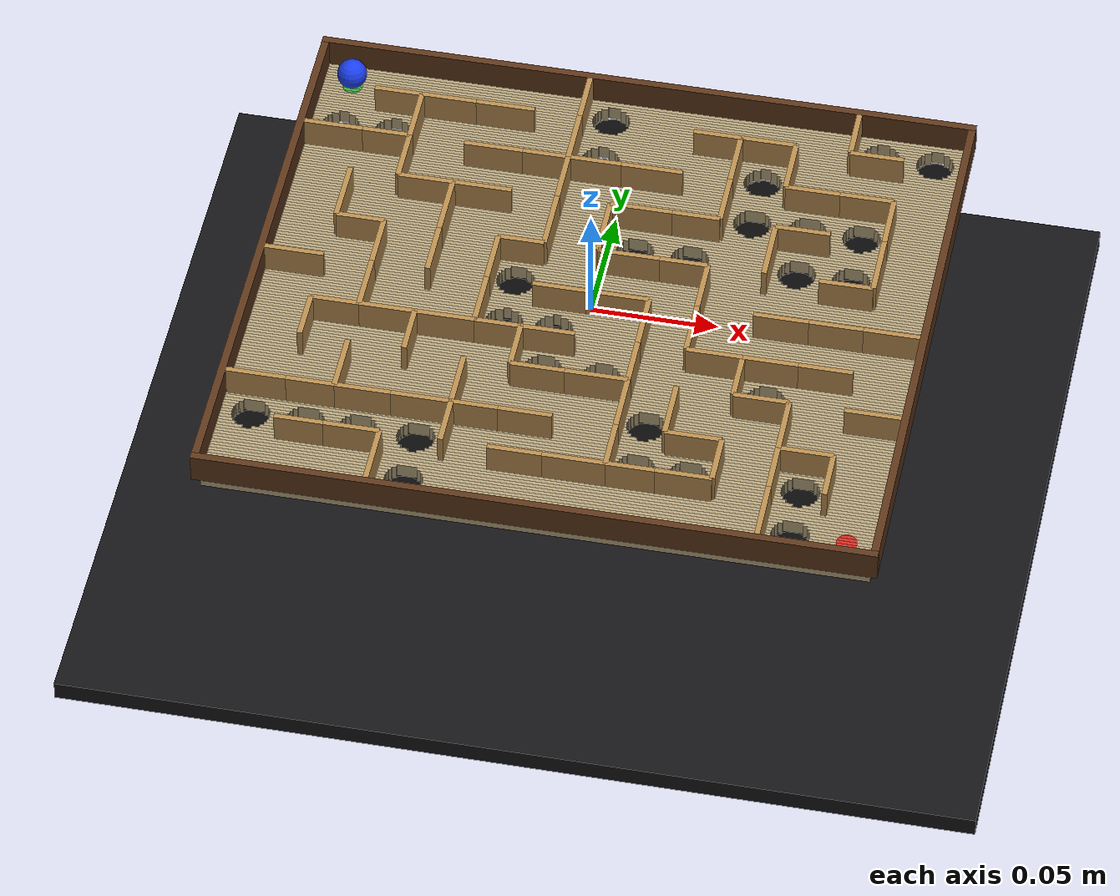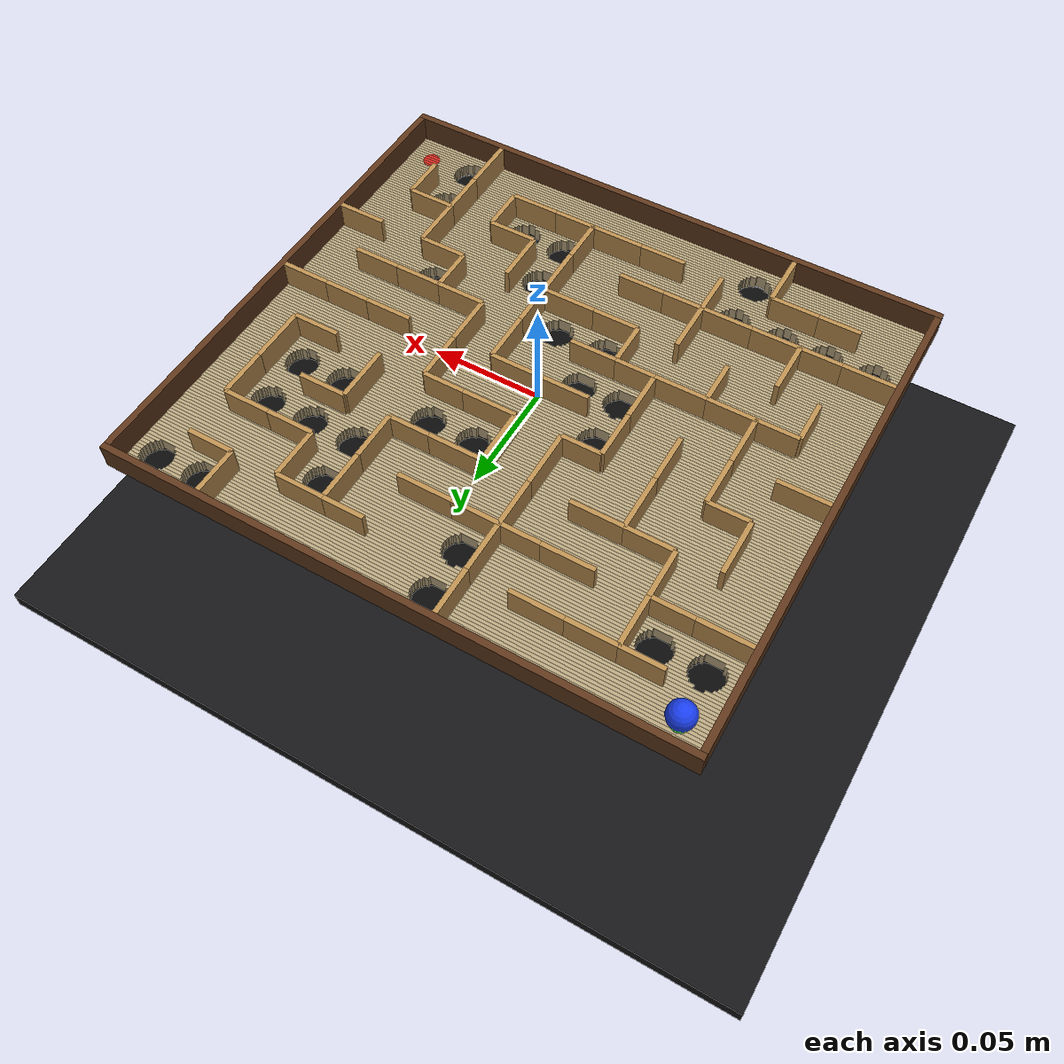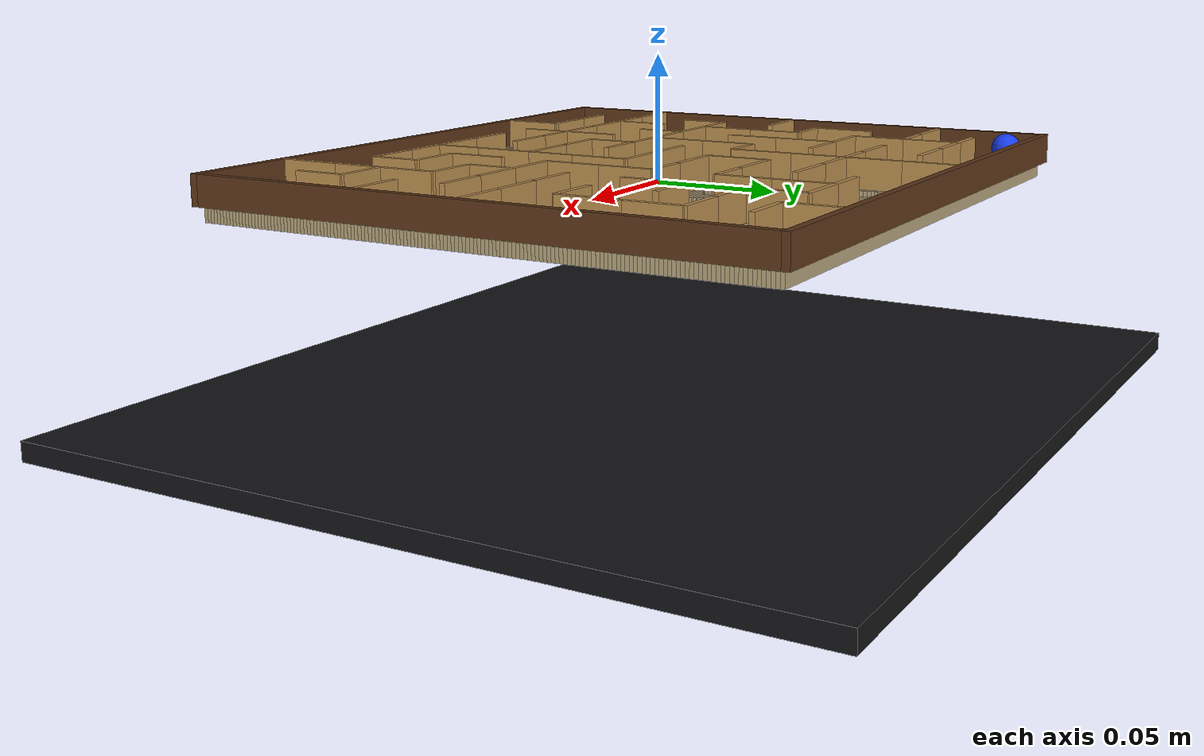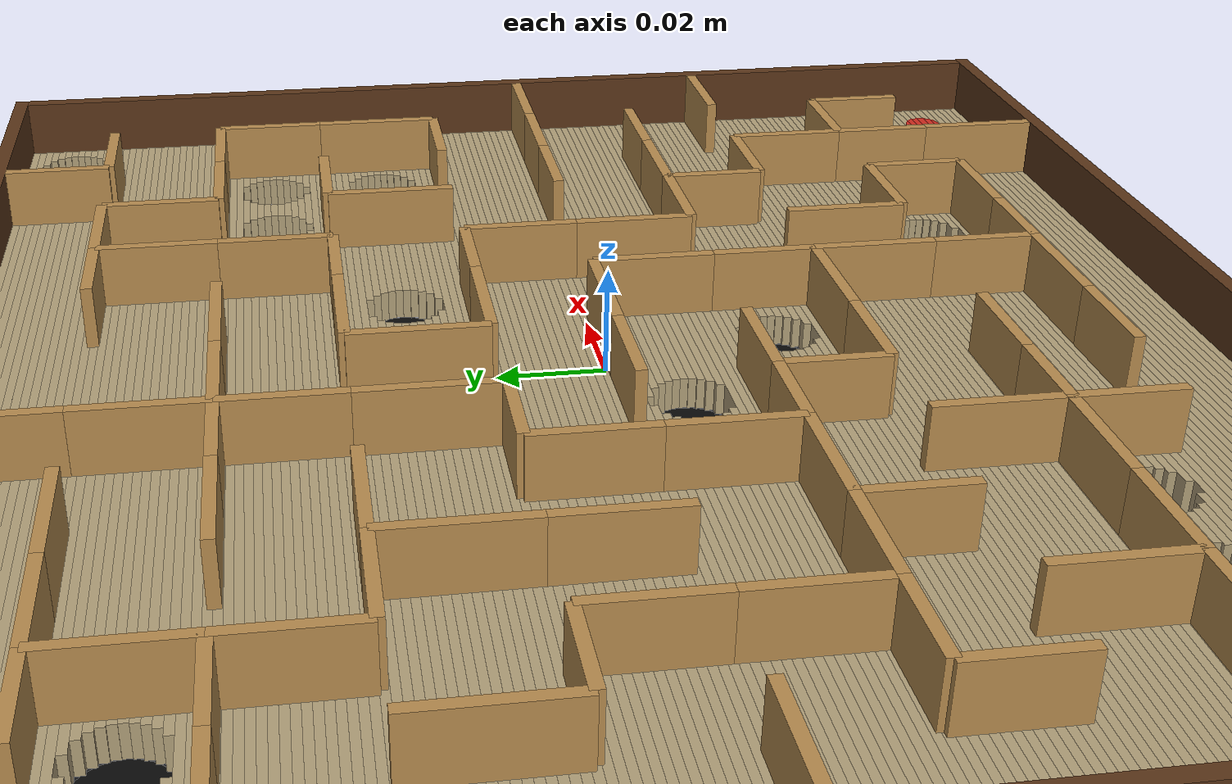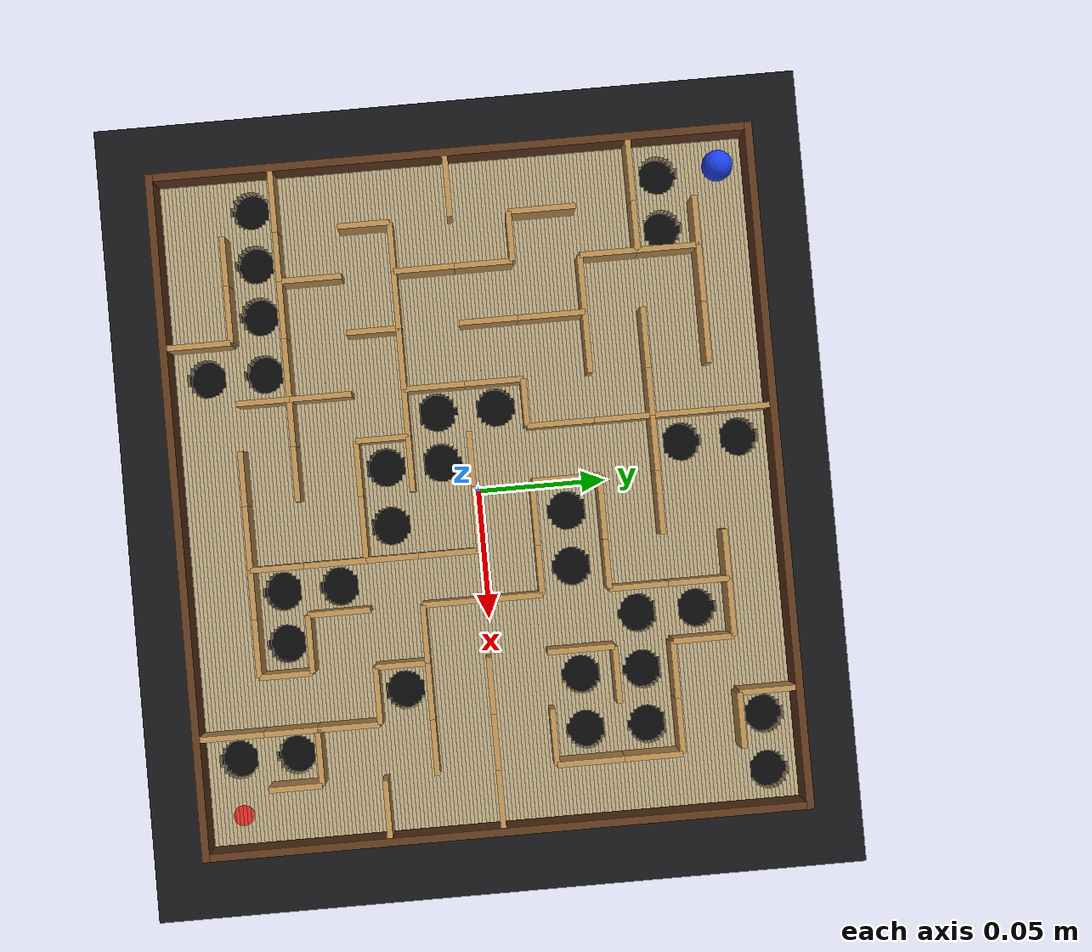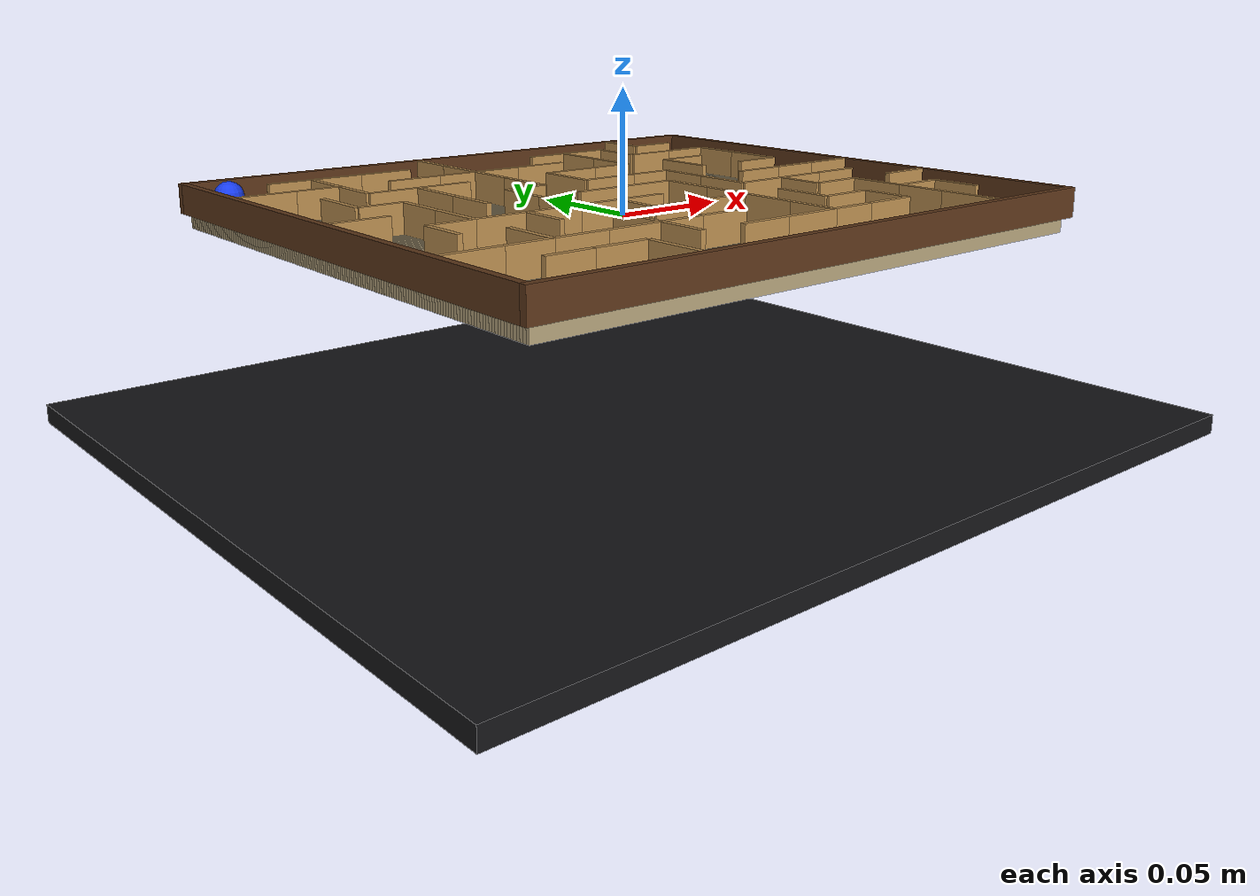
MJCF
<mujoco model="tag_custom_maze">
  <compiler angle="radian" inertiafromgeom="auto"/>
  <option timestep="0.001" gravity="0 0 -9.81" integrator="implicitfast" solver="Newton" iterations="12" tolerance="1e-9"/>
  <size nconmax="4000" njmax="12000"/>
  <visual>
    <global offwidth="900" offheight="800"/>
    <quality shadowsize="2048"/>
    <map znear="0.01" zfar="3"/>
  </visual>
  <default>
    <default class="floor">
      <geom friction="0.30 0.015 0.002" solref="0.004 1" solimp="0.95 0.99 0.001" density="650"/>
    </default>
    <default class="wall">
      <geom friction="0.35 0.02 0.003" solref="0.003 1" solimp="0.95 0.99 0.001" density="700"/>
    </default>
  </default>
  <worldbody>
    <light name="key" pos="0 -0.15 0.55" dir="0 0 -1" diffuse="0.9 0.9 0.9"/>
    <light name="fill" pos="-0.25 0.2 0.35" dir="0.4 -0.3 -1" diffuse="0.45 0.45 0.45"/>
    <camera name="top" pos="0 0 0.43" quat="1 0 0 0" mode="fixed" fovy="37"/>
    <geom name="catch_tray" type="box" pos="0 0 -0.085" size="0.18 0.16 0.004" rgba="0.08 0.08 0.09 1" friction="0.5 0.02 0.003"/>
    <body name="tilt_x_frame" pos="0 0 0">
      <inertial pos="0 0 0" mass="0.02" diaginertia="0.0001 0.0001 0.0001"/>
      <joint name="tilt_x" type="hinge" axis="1 0 0" range="-0.174532925 0.174532925" damping="0.8" armature="0.01"/>
      <body name="board" pos="0 0 0">
        <joint name="tilt_y" type="hinge" axis="0 1 0" range="-0.174532925 0.174532925" damping="0.8" armature="0.01"/>
        <geom name="floor_0" type="box" pos="0 -0.113751634 -0.003" size="0.1295 0.000748366013 0.003" rgba="0.70 0.63 0.48 1" class="floor"/><geom name="floor_1" type="box" pos="0 -0.112254902 -0.003" size="0.1295 0.000748366013 0.003" rgba="0.70 0.63 0.48 1" class="floor"/><geom name="floor_2" type="box" pos="0 -0.11075817 -0.003" size="0.1295 0.000748366013 0.003" rgba="0.70 0.63 0.48 1" class="floor"/><geom name="floor_3" type="box" pos="-0.0924305159 -0.109261438 -0.003" size="0.0370694841 0.000748366013 0.003" rgba="0.70 0.63 0.48 1" class="floor"/><geom name="floor_4" type="box" pos="0.0217902375 -0.109261438 -0.003" size="0.0724534552 0.000748366013 0.003" rgba="0.70 0.63 0.48 1" class="floor"/><geom name="floor_5" type="box" pos="0.114220753 -0.109261438 -0.003" size="0.0152792466 0.000748366013 0.003" rgba="0.70 0.63 0.48 1" class="floor"/><geom name="floor_6" type="box" pos="-0.0937359141 -0.107764706 -0.003" size="0.0357640859 0.000748366013 0.003" rgba="0.70 0.63 0.48 1" class="floor"/><geom name="floor_7" type="box" pos="0.0217902375 -0.107764706 -0.003" size="0.0698426589 0.000748366013 0.003" rgba="0.70 0.63 0.48 1" class="floor"/><geom name="floor_8" type="box" pos="0.115526152 -0.107764706 -0.003" size="0.0139738484 0.000748366013 0.003" rgba="0.70 0.63 0.48 1" class="floor"/><geom name="floor_9" type="box" pos="-0.0943865391 -0.106267974 -0.003" size="0.0351134609 0.000748366013 0.003" rgba="0.70 0.63 0.48 1" class="floor"/><geom name="floor_10" type="box" pos="0.0217902375 -0.106267974 -0.003" size="0.0685414088 0.000748366013 0.003" rgba="0.70 0.63 0.48 1" class="floor"/><geom name="floor_11" type="box" pos="0.116176777 -0.106267974 -0.003" size="0.0133232234 0.000748366013 0.003" rgba="0.70 0.63 0.48 1" class="floor"/><geom name="floor_12" type="box" pos="-0.0947674725 -0.104771242 -0.003" size="0.0347325275 0.000748366013 0.003" rgba="0.70 0.63 0.48 1" class="floor"/><geom name="floor_13" type="box" pos="0.0217902375 -0.104771242 -0.003" size="0.067779542 0.000748366013 0.003" rgba="0.70 0.63 0.48 1" class="floor"/><geom name="floor_14" type="box" pos="0.11655771 -0.104771242 -0.003" size="0.01294229 0.000748366013 0.003" rgba="0.70 0.63 0.48 1" class="floor"/><geom name="floor_15" type="box" pos="-0.0949628149 -0.10327451 -0.003" size="0.0345371851 0.000748366013 0.003" rgba="0.70 0.63 0.48 1" class="floor"/><geom name="floor_16" type="box" pos="0.0217902375 -0.10327451 -0.003" size="0.0673888572 0.000748366013 0.003" rgba="0.70 0.63 0.48 1" class="floor"/><geom name="floor_17" type="box" pos="0.116753052 -0.10327451 -0.003" size="0.0127469476 0.000748366013 0.003" rgba="0.70 0.63 0.48 1" class="floor"/><geom name="floor_18" type="box" pos="-0.0950017164 -0.101777778 -0.003" size="0.0344982836 0.000748366013 0.003" rgba="0.70 0.63 0.48 1" class="floor"/><geom name="floor_19" type="box" pos="0.0217902375 -0.101777778 -0.003" size="0.0673110542 0.000748366013 0.003" rgba="0.70 0.63 0.48 1" class="floor"/><geom name="floor_20" type="box" pos="0.116791954 -0.101777778 -0.003" size="0.0127080461 0.000748366013 0.003" rgba="0.70 0.63 0.48 1" class="floor"/><geom name="floor_21" type="box" pos="-0.0948892057 -0.100281046 -0.003" size="0.0346107943 0.000748366013 0.003" rgba="0.70 0.63 0.48 1" class="floor"/><geom name="floor_22" type="box" pos="0.0217902375 -0.100281046 -0.003" size="0.0675360756 0.000748366013 0.003" rgba="0.70 0.63 0.48 1" class="floor"/><geom name="floor_23" type="box" pos="0.116679443 -0.100281046 -0.003" size="0.0128205567 0.000748366013 0.003" rgba="0.70 0.63 0.48 1" class="floor"/><geom name="floor_24" type="box" pos="-0.0946100799 -0.0987843137 -0.003" size="0.0348899201 0.000748366013 0.003" rgba="0.70 0.63 0.48 1" class="floor"/><geom name="floor_25" type="box" pos="0.0217902375 -0.0987843137 -0.003" size="0.0680943272 0.000748366013 0.003" rgba="0.70 0.63 0.48 1" class="floor"/><geom name="floor_26" type="box" pos="0.116400317 -0.0987843137 -0.003" size="0.0130996825 0.000748366013 0.003" rgba="0.70 0.63 0.48 1" class="floor"/><geom name="floor_27" type="box" pos="-0.0941159633 -0.0972875817 -0.003" size="0.0353840367 0.000748366013 0.003" rgba="0.70 0.63 0.48 1" class="floor"/><geom name="floor_28" type="box" pos="0.0217902375 -0.0972875817 -0.003" size="0.0690825604 0.000748366013 0.003" rgba="0.70 0.63 0.48 1" class="floor"/><geom name="floor_29" type="box" pos="0.115906201 -0.0972875817 -0.003" size="0.0135937992 0.000748366013 0.003" rgba="0.70 0.63 0.48 1" class="floor"/><geom name="floor_30" type="box" pos="-0.0932531928 -0.0957908497 -0.003" size="0.0362468072 0.000748366013 0.003" rgba="0.70 0.63 0.48 1" class="floor"/><geom name="floor_31" type="box" pos="0.0217902375 -0.0957908497 -0.003" size="0.0708081015 0.000748366013 0.003" rgba="0.70 0.63 0.48 1" class="floor"/><geom name="floor_32" type="box" pos="0.11504343 -0.0957908497 -0.003" size="0.0144565697 0.000748366013 0.003" rgba="0.70 0.63 0.48 1" class="floor"/><geom name="floor_33" type="box" pos="0 -0.0942941176 -0.003" size="0.1295 0.000748366013 0.003" rgba="0.70 0.63 0.48 1" class="floor"/><geom name="floor_34" type="box" pos="0 -0.0927973856 -0.003" size="0.1295 0.000748366013 0.003" rgba="0.70 0.63 0.48 1" class="floor"/><geom name="floor_35" type="box" pos="0 -0.0913006536 -0.003" size="0.1295 0.000748366013 0.003" rgba="0.70 0.63 0.48 1" class="floor"/><geom name="floor_36" type="box" pos="0 -0.0898039216 -0.003" size="0.1295 0.000748366013 0.003" rgba="0.70 0.63 0.48 1" class="floor"/><geom name="floor_37" type="box" pos="0 -0.0883071895 -0.003" size="0.1295 0.000748366013 0.003" rgba="0.70 0.63 0.48 1" class="floor"/><geom name="floor_38" type="box" pos="-0.124518685 -0.0868104575 -0.003" size="0.00498131537 0.000748366013 0.003" rgba="0.70 0.63 0.48 1" class="floor"/><geom name="floor_39" type="box" pos="-0.107070803 -0.0868104575 -0.003" size="0.00885976556 0.000748366013 0.003" rgba="0.70 0.63 0.48 1" class="floor"/><geom name="floor_40" type="box" pos="-0.0861206702 -0.0868104575 -0.003" size="0.00848356704 0.000748366013 0.003" rgba="0.70 0.63 0.48 1" class="floor"/><geom name="floor_41" type="box" pos="-0.0644229138 -0.0868104575 -0.003" size="0.00960738884 0.000748366013 0.003" rgba="0.70 0.63 0.48 1" class="floor"/><geom name="floor_42" type="box" pos="-0.010250882 -0.0868104575 -0.003" size="0.0409578426 0.000748366013 0.003" rgba="0.70 0.63 0.48 1" class="floor"/><geom name="floor_43" type="box" pos="0.0427861596 -0.0868104575 -0.003" size="0.00847239851 0.000748366013 0.003" rgba="0.70 0.63 0.48 1" class="floor"/><geom name="floor_44" type="box" pos="0.0748272791 -0.0868104575 -0.003" size="0.0199619205 0.000748366013 0.003" rgba="0.70 0.63 0.48 1" class="floor"/><geom name="floor_45" type="box" pos="0.113948 -0.0868104575 -0.003" size="0.015552 0.000748366013 0.003" rgba="0.70 0.63 0.48 1" class="floor"/><geom name="floor_46" type="box" pos="-0.126004678 -0.0853137255 -0.003" size="0.00349532153 0.000748366013 0.003" rgba="0.70 0.63 0.48 1" class="floor"/><geom name="floor_47" type="box" pos="-0.107070803 -0.0853137255 -0.003" size="0.00588777787 0.000748366013 0.003" rgba="0.70 0.63 0.48 1" class="floor"/><geom name="floor_48" type="box" pos="-0.0861206702 -0.0853137255 -0.003" size="0.00551157935 0.000748366013 0.003" rgba="0.70 0.63 0.48 1" class="floor"/><geom name="floor_49" type="box" pos="-0.0644229138 -0.0853137255 -0.003" size="0.00663540115 0.000748366013 0.003" rgba="0.70 0.63 0.48 1" class="floor"/><geom name="floor_50" type="box" pos="-0.010250882 -0.0853137255 -0.003" size="0.0379858549 0.000748366013 0.003" rgba="0.70 0.63 0.48 1" class="floor"/><geom name="floor_51" type="box" pos="0.0427861596 -0.0853137255 -0.003" size="0.00550041082 0.000748366013 0.003" rgba="0.70 0.63 0.48 1" class="floor"/><geom name="floor_52" type="box" pos="0.0748272791 -0.0853137255 -0.003" size="0.0169899328 0.000748366013 0.003" rgba="0.70 0.63 0.48 1" class="floor"/><geom name="floor_53" type="box" pos="0.115433994 -0.0853137255 -0.003" size="0.0140660061 0.000748366013 0.003" rgba="0.70 0.63 0.48 1" class="floor"/><geom name="floor_54" type="box" pos="-0.126694158 -0.0838169935 -0.003" size="0.00280584171 0.000748366013 0.003" rgba="0.70 0.63 0.48 1" class="floor"/><geom name="floor_55" type="box" pos="-0.107070803 -0.0838169935 -0.003" size="0.00450881825 0.000748366013 0.003" rgba="0.70 0.63 0.48 1" class="floor"/><geom name="floor_56" type="box" pos="-0.0861206702 -0.0838169935 -0.003" size="0.00413261973 0.000748366013 0.003" rgba="0.70 0.63 0.48 1" class="floor"/><geom name="floor_57" type="box" pos="-0.0644229138 -0.0838169935 -0.003" size="0.00525644153 0.000748366013 0.003" rgba="0.70 0.63 0.48 1" class="floor"/><geom name="floor_58" type="box" pos="-0.010250882 -0.0838169935 -0.003" size="0.0366068952 0.000748366013 0.003" rgba="0.70 0.63 0.48 1" class="floor"/><geom name="floor_59" type="box" pos="0.0427861596 -0.0838169935 -0.003" size="0.0041214512 0.000748366013 0.003" rgba="0.70 0.63 0.48 1" class="floor"/><geom name="floor_60" type="box" pos="0.0748272791 -0.0838169935 -0.003" size="0.0156109732 0.000748366013 0.003" rgba="0.70 0.63 0.48 1" class="floor"/><geom name="floor_61" type="box" pos="0.116123474 -0.0838169935 -0.003" size="0.0133765263 0.000748366013 0.003" rgba="0.70 0.63 0.48 1" class="floor"/><geom name="floor_62" type="box" pos="-0.127097906 -0.0823202614 -0.003" size="0.00240209448 0.000748366013 0.003" rgba="0.70 0.63 0.48 1" class="floor"/><geom name="floor_63" type="box" pos="-0.107070803 -0.0823202614 -0.003" size="0.00370132379 0.000748366013 0.003" rgba="0.70 0.63 0.48 1" class="floor"/><geom name="floor_64" type="box" pos="-0.0861206702 -0.0823202614 -0.003" size="0.00332512527 0.000748366013 0.003" rgba="0.70 0.63 0.48 1" class="floor"/><geom name="floor_65" type="box" pos="-0.0644229138 -0.0823202614 -0.003" size="0.00444894707 0.000748366013 0.003" rgba="0.70 0.63 0.48 1" class="floor"/><geom name="floor_66" type="box" pos="-0.010250882 -0.0823202614 -0.003" size="0.0357994008 0.000748366013 0.003" rgba="0.70 0.63 0.48 1" class="floor"/><geom name="floor_67" type="box" pos="0.0427861596 -0.0823202614 -0.003" size="0.00331395674 0.000748366013 0.003" rgba="0.70 0.63 0.48 1" class="floor"/><geom name="floor_68" type="box" pos="0.0748272791 -0.0823202614 -0.003" size="0.0148034787 0.000748366013 0.003" rgba="0.70 0.63 0.48 1" class="floor"/><geom name="floor_69" type="box" pos="0.116527221 -0.0823202614 -0.003" size="0.0129727791 0.000748366013 0.003" rgba="0.70 0.63 0.48 1" class="floor"/><geom name="floor_70" type="box" pos="-0.127310833 -0.0808235294 -0.003" size="0.00218916651 0.000748366013 0.003" rgba="0.70 0.63 0.48 1" class="floor"/><geom name="floor_71" type="box" pos="-0.107070803 -0.0808235294 -0.003" size="0.00327546785 0.000748366013 0.003" rgba="0.70 0.63 0.48 1" class="floor"/><geom name="floor_72" type="box" pos="-0.0861206702 -0.0808235294 -0.003" size="0.00289926933 0.000748366013 0.003" rgba="0.70 0.63 0.48 1" class="floor"/><geom name="floor_73" type="box" pos="-0.0644229138 -0.0808235294 -0.003" size="0.00402309112 0.000748366013 0.003" rgba="0.70 0.63 0.48 1" class="floor"/><geom name="floor_74" type="box" pos="-0.010250882 -0.0808235294 -0.003" size="0.0353735448 0.000748366013 0.003" rgba="0.70 0.63 0.48 1" class="floor"/><geom name="floor_75" type="box" pos="0.0427861596 -0.0808235294 -0.003" size="0.00288810079 0.000748366013 0.003" rgba="0.70 0.63 0.48 1" class="floor"/><geom name="floor_76" type="box" pos="0.0748272791 -0.0808235294 -0.003" size="0.0143776228 0.000748366013 0.003" rgba="0.70 0.63 0.48 1" class="floor"/><geom name="floor_77" type="box" pos="0.116740149 -0.0808235294 -0.003" size="0.0127598511 0.000748366013 0.003" rgba="0.70 0.63 0.48 1" class="floor"/><geom name="floor_78" type="box" pos="-0.127365601 -0.0793267974 -0.003" size="0.00213439893 0.000748366013 0.003" rgba="0.70 0.63 0.48 1" class="floor"/><geom name="floor_79" type="box" pos="-0.107070803 -0.0793267974 -0.003" size="0.00316593268 0.000748366013 0.003" rgba="0.70 0.63 0.48 1" class="floor"/><geom name="floor_80" type="box" pos="-0.0861206702 -0.0793267974 -0.003" size="0.00278973417 0.000748366013 0.003" rgba="0.70 0.63 0.48 1" class="floor"/><geom name="floor_81" type="box" pos="-0.0644229138 -0.0793267974 -0.003" size="0.00391355596 0.000748366013 0.003" rgba="0.70 0.63 0.48 1" class="floor"/><geom name="floor_82" type="box" pos="-0.010250882 -0.0793267974 -0.003" size="0.0352640097 0.000748366013 0.003" rgba="0.70 0.63 0.48 1" class="floor"/><geom name="floor_83" type="box" pos="0.0427861596 -0.0793267974 -0.003" size="0.00277856563 0.000748366013 0.003" rgba="0.70 0.63 0.48 1" class="floor"/><geom name="floor_84" type="box" pos="0.0748272791 -0.0793267974 -0.003" size="0.0142680876 0.000748366013 0.003" rgba="0.70 0.63 0.48 1" class="floor"/><geom name="floor_85" type="box" pos="0.116794916 -0.0793267974 -0.003" size="0.0127050835 0.000748366013 0.003" rgba="0.70 0.63 0.48 1" class="floor"/><geom name="floor_86" type="box" pos="-0.12726933 -0.0778300654 -0.003" size="0.00223066987 0.000748366013 0.003" rgba="0.70 0.63 0.48 1" class="floor"/><geom name="floor_87" type="box" pos="-0.107070803 -0.0778300654 -0.003" size="0.00335847455 0.000748366013 0.003" rgba="0.70 0.63 0.48 1" class="floor"/><geom name="floor_88" type="box" pos="-0.0861206702 -0.0778300654 -0.003" size="0.00298227603 0.000748366013 0.003" rgba="0.70 0.63 0.48 1" class="floor"/><geom name="floor_89" type="box" pos="-0.0644229138 -0.0778300654 -0.003" size="0.00410609783 0.000748366013 0.003" rgba="0.70 0.63 0.48 1" class="floor"/><geom name="floor_90" type="box" pos="-0.010250882 -0.0778300654 -0.003" size="0.0354565516 0.000748366013 0.003" rgba="0.70 0.63 0.48 1" class="floor"/><geom name="floor_91" type="box" pos="0.0427861596 -0.0778300654 -0.003" size="0.0029711075 0.000748366013 0.003" rgba="0.70 0.63 0.48 1" class="floor"/><geom name="floor_92" type="box" pos="0.0748272791 -0.0778300654 -0.003" size="0.0144606295 0.000748366013 0.003" rgba="0.70 0.63 0.48 1" class="floor"/><geom name="floor_93" type="box" pos="0.116698646 -0.0778300654 -0.003" size="0.0128013545 0.000748366013 0.003" rgba="0.70 0.63 0.48 1" class="floor"/><geom name="floor_94" type="box" pos="-0.127009186 -0.0763333333 -0.003" size="0.00249081449 0.000748366013 0.003" rgba="0.70 0.63 0.48 1" class="floor"/><geom name="floor_95" type="box" pos="-0.107070803 -0.0763333333 -0.003" size="0.0038787638 0.000748366013 0.003" rgba="0.70 0.63 0.48 1" class="floor"/><geom name="floor_96" type="box" pos="-0.0861206702 -0.0763333333 -0.003" size="0.00350256528 0.000748366013 0.003" rgba="0.70 0.63 0.48 1" class="floor"/><geom name="floor_97" type="box" pos="-0.0644229138 -0.0763333333 -0.003" size="0.00462638707 0.000748366013 0.003" rgba="0.70 0.63 0.48 1" class="floor"/><geom name="floor_98" type="box" pos="-0.010250882 -0.0763333333 -0.003" size="0.0359768408 0.000748366013 0.003" rgba="0.70 0.63 0.48 1" class="floor"/><geom name="floor_99" type="box" pos="0.0427861596 -0.0763333333 -0.003" size="0.00349139674 0.000748366013 0.003" rgba="0.70 0.63 0.48 1" class="floor"/><geom name="floor_100" type="box" pos="0.0748272791 -0.0763333333 -0.003" size="0.0149809187 0.000748366013 0.003" rgba="0.70 0.63 0.48 1" class="floor"/><geom name="floor_101" type="box" pos="0.116438501 -0.0763333333 -0.003" size="0.0130614991 0.000748366013 0.003" rgba="0.70 0.63 0.48 1" class="floor"/><geom name="floor_102" type="box" pos="-0.126541762 -0.0748366013 -0.003" size="0.00295823801 0.000748366013 0.003" rgba="0.70 0.63 0.48 1" class="floor"/><geom name="floor_103" type="box" pos="-0.107070803 -0.0748366013 -0.003" size="0.00481361083 0.000748366013 0.003" rgba="0.70 0.63 0.48 1" class="floor"/><geom name="floor_104" type="box" pos="-0.0861206702 -0.0748366013 -0.003" size="0.00443741231 0.000748366013 0.003" rgba="0.70 0.63 0.48 1" class="floor"/><geom name="floor_105" type="box" pos="-0.0644229138 -0.0748366013 -0.003" size="0.00556123411 0.000748366013 0.003" rgba="0.70 0.63 0.48 1" class="floor"/><geom name="floor_106" type="box" pos="-0.010250882 -0.0748366013 -0.003" size="0.0369116878 0.000748366013 0.003" rgba="0.70 0.63 0.48 1" class="floor"/><geom name="floor_107" type="box" pos="0.0427861596 -0.0748366013 -0.003" size="0.00442624378 0.000748366013 0.003" rgba="0.70 0.63 0.48 1" class="floor"/><geom name="floor_108" type="box" pos="0.0748272791 -0.0748366013 -0.003" size="0.0159157658 0.000748366013 0.003" rgba="0.70 0.63 0.48 1" class="floor"/><geom name="floor_109" type="box" pos="0.115971077 -0.0748366013 -0.003" size="0.0135289226 0.000748366013 0.003" rgba="0.70 0.63 0.48 1" class="floor"/><geom name="floor_110" type="box" pos="-0.125733944 -0.0733398693 -0.003" size="0.00376605643 0.000748366013 0.003" rgba="0.70 0.63 0.48 1" class="floor"/><geom name="floor_111" type="box" pos="-0.107070803 -0.0733398693 -0.003" size="0.00642924769 0.000748366013 0.003" rgba="0.70 0.63 0.48 1" class="floor"/><geom name="floor_112" type="box" pos="-0.0861206702 -0.0733398693 -0.003" size="0.00605304917 0.000748366013 0.003" rgba="0.70 0.63 0.48 1" class="floor"/><geom name="floor_113" type="box" pos="-0.0644229138 -0.0733398693 -0.003" size="0.00717687096 0.000748366013 0.003" rgba="0.70 0.63 0.48 1" class="floor"/><geom name="floor_114" type="box" pos="-0.010250882 -0.0733398693 -0.003" size="0.0385273247 0.000748366013 0.003" rgba="0.70 0.63 0.48 1" class="floor"/><geom name="floor_115" type="box" pos="0.0427861596 -0.0733398693 -0.003" size="0.00604188063 0.000748366013 0.003" rgba="0.70 0.63 0.48 1" class="floor"/><geom name="floor_116" type="box" pos="0.0748272791 -0.0733398693 -0.003" size="0.0175314026 0.000748366013 0.003" rgba="0.70 0.63 0.48 1" class="floor"/><geom name="floor_117" type="box" pos="0.115163259 -0.0733398693 -0.003" size="0.014336741 0.000748366013 0.003" rgba="0.70 0.63 0.48 1" class="floor"/><geom name="floor_118" type="box" pos="0 -0.0718431373 -0.003" size="0.1295 0.000748366013 0.003" rgba="0.70 0.63 0.48 1" class="floor"/><geom name="floor_119" type="box" pos="0 -0.0703464052 -0.003" size="0.1295 0.000748366013 0.003" rgba="0.70 0.63 0.48 1" class="floor"/><geom name="floor_120" type="box" pos="0 -0.0688496732 -0.003" size="0.1295 0.000748366013 0.003" rgba="0.70 0.63 0.48 1" class="floor"/><geom name="floor_121" type="box" pos="0 -0.0673529412 -0.003" size="0.1295 0.000748366013 0.003" rgba="0.70 0.63 0.48 1" class="floor"/><geom name="floor_122" type="box" pos="0 -0.0658562092 -0.003" size="0.1295 0.000748366013 0.003" rgba="0.70 0.63 0.48 1" class="floor"/><geom name="floor_123" type="box" pos="-0.0496364606 -0.0643594771 -0.003" size="0.0798635394 0.000748366013 0.003" rgba="0.70 0.63 0.48 1" class="floor"/><geom name="floor_124" type="box" pos="0.0821468214 -0.0643594771 -0.003" size="0.0473531786 0.000748366013 0.003" rgba="0.70 0.63 0.48 1" class="floor"/><geom name="floor_125" type="box" pos="-0.0509625338 -0.0628627451 -0.003" size="0.0785374662 0.000748366013 0.003" rgba="0.70 0.63 0.48 1" class="floor"/><geom name="floor_126" type="box" pos="0.0834728946 -0.0628627451 -0.003" size="0.0460271054 0.000748366013 0.003" rgba="0.70 0.63 0.48 1" class="floor"/><geom name="floor_127" type="box" pos="-0.0516182439 -0.0613660131 -0.003" size="0.0778817561 0.000748366013 0.003" rgba="0.70 0.63 0.48 1" class="floor"/><geom name="floor_128" type="box" pos="0.0841286047 -0.0613660131 -0.003" size="0.0453713953 0.000748366013 0.003" rgba="0.70 0.63 0.48 1" class="floor"/><geom name="floor_129" type="box" pos="-0.0520022177 -0.059869281 -0.003" size="0.0774977823 0.000748366013 0.003" rgba="0.70 0.63 0.48 1" class="floor"/><geom name="floor_130" type="box" pos="0.0845125785 -0.059869281 -0.003" size="0.0449874215 0.000748366013 0.003" rgba="0.70 0.63 0.48 1" class="floor"/><geom name="floor_131" type="box" pos="-0.0521999243 -0.058372549 -0.003" size="0.0773000757 0.000748366013 0.003" rgba="0.70 0.63 0.48 1" class="floor"/><geom name="floor_132" type="box" pos="0.0847102851 -0.058372549 -0.003" size="0.0447897149 0.000748366013 0.003" rgba="0.70 0.63 0.48 1" class="floor"/><geom name="floor_133" type="box" pos="-0.0522409718 -0.056875817 -0.003" size="0.0772590282 0.000748366013 0.003" rgba="0.70 0.63 0.48 1" class="floor"/><geom name="floor_134" type="box" pos="0.0847513326 -0.056875817 -0.003" size="0.0447486674 0.000748366013 0.003" rgba="0.70 0.63 0.48 1" class="floor"/><geom name="floor_135" type="box" pos="-0.0521306701 -0.055379085 -0.003" size="0.0773693299 0.000748366013 0.003" rgba="0.70 0.63 0.48 1" class="floor"/><geom name="floor_136" type="box" pos="0.0846410309 -0.055379085 -0.003" size="0.0448589691 0.000748366013 0.003" rgba="0.70 0.63 0.48 1" class="floor"/><geom name="floor_137" type="box" pos="-0.0518541436 -0.0538823529 -0.003" size="0.0776458564 0.000748366013 0.003" rgba="0.70 0.63 0.48 1" class="floor"/><geom name="floor_138" type="box" pos="0.0843645044 -0.0538823529 -0.003" size="0.0451354956 0.000748366013 0.003" rgba="0.70 0.63 0.48 1" class="floor"/><geom name="floor_139" type="box" pos="-0.0513637224 -0.0523856209 -0.003" size="0.0781362776 0.000748366013 0.003" rgba="0.70 0.63 0.48 1" class="floor"/><geom name="floor_140" type="box" pos="0.0838740832 -0.0523856209 -0.003" size="0.0456259168 0.000748366013 0.003" rgba="0.70 0.63 0.48 1" class="floor"/><geom name="floor_141" type="box" pos="-0.0505087822 -0.0508888889 -0.003" size="0.0789912178 0.000748366013 0.003" rgba="0.70 0.63 0.48 1" class="floor"/><geom name="floor_142" type="box" pos="0.083019143 -0.0508888889 -0.003" size="0.046480857 0.000748366013 0.003" rgba="0.70 0.63 0.48 1" class="floor"/><geom name="floor_143" type="box" pos="0 -0.0493921569 -0.003" size="0.1295 0.000748366013 0.003" rgba="0.70 0.63 0.48 1" class="floor"/><geom name="floor_144" type="box" pos="0 -0.0478954248 -0.003" size="0.1295 0.000748366013 0.003" rgba="0.70 0.63 0.48 1" class="floor"/><geom name="floor_145" type="box" pos="0 -0.0463986928 -0.003" size="0.1295 0.000748366013 0.003" rgba="0.70 0.63 0.48 1" class="floor"/><geom name="floor_146" type="box" pos="0 -0.0449019608 -0.003" size="0.1295 0.000748366013 0.003" rgba="0.70 0.63 0.48 1" class="floor"/><geom name="floor_147" type="box" pos="0 -0.0434052288 -0.003" size="0.1295 0.000748366013 0.003" rgba="0.70 0.63 0.48 1" class="floor"/><geom name="floor_148" type="box" pos="-0.0724825435 -0.0419084967 -0.003" size="0.0570174565 0.000748366013 0.003" rgba="0.70 0.63 0.48 1" class="floor"/><geom name="floor_149" type="box" pos="-0.000836287435 -0.0419084967 -0.003" size="0.0083716779 0.000748366013 0.003" rgba="0.70 0.63 0.48 1" class="floor"/><geom name="floor_150" type="box" pos="0.0428402232 -0.0419084967 -0.003" size="0.029047711 0.000748366013 0.003" rgba="0.70 0.63 0.48 1" class="floor"/><geom name="floor_151" type="box" pos="0.103822528 -0.0419084967 -0.003" size="0.0256774721 0.000748366013 0.003" rgba="0.70 0.63 0.48 1" class="floor"/><geom name="floor_152" type="box" pos="-0.073561749 -0.0404117647 -0.003" size="0.055938251 0.000748366013 0.003" rgba="0.70 0.63 0.48 1" class="floor"/><geom name="floor_153" type="box" pos="-0.000836287435 -0.0404117647 -0.003" size="0.00621326698 0.000748366013 0.003" rgba="0.70 0.63 0.48 1" class="floor"/><geom name="floor_154" type="box" pos="0.0428402232 -0.0404117647 -0.003" size="0.0268893 0.000748366013 0.003" rgba="0.70 0.63 0.48 1" class="floor"/><geom name="floor_155" type="box" pos="0.104901733 -0.0404117647 -0.003" size="0.0245982666 0.000748366013 0.003" rgba="0.70 0.63 0.48 1" class="floor"/><geom name="floor_156" type="box" pos="-0.0741445549 -0.0389150327 -0.003" size="0.0553554451 0.000748366013 0.003" rgba="0.70 0.63 0.48 1" class="floor"/><geom name="floor_157" type="box" pos="-0.000836287435 -0.0389150327 -0.003" size="0.00504765519 0.000748366013 0.003" rgba="0.70 0.63 0.48 1" class="floor"/><geom name="floor_158" type="box" pos="0.0428402232 -0.0389150327 -0.003" size="0.0257236883 0.000748366013 0.003" rgba="0.70 0.63 0.48 1" class="floor"/><geom name="floor_159" type="box" pos="0.105484539 -0.0389150327 -0.003" size="0.0240154607 0.000748366013 0.003" rgba="0.70 0.63 0.48 1" class="floor"/><geom name="floor_160" type="box" pos="-0.0744833432 -0.0374183007 -0.003" size="0.0550166568 0.000748366013 0.003" rgba="0.70 0.63 0.48 1" class="floor"/><geom name="floor_161" type="box" pos="-0.000836287435 -0.0374183007 -0.003" size="0.0043700785 0.000748366013 0.003" rgba="0.70 0.63 0.48 1" class="floor"/><geom name="floor_162" type="box" pos="0.0428402232 -0.0374183007 -0.003" size="0.0250461116 0.000748366013 0.003" rgba="0.70 0.63 0.48 1" class="floor"/><geom name="floor_163" type="box" pos="0.105823328 -0.0374183007 -0.003" size="0.0236766724 0.000748366013 0.003" rgba="0.70 0.63 0.48 1" class="floor"/><geom name="floor_164" type="box" pos="-0.0746452633 -0.0359215686 -0.003" size="0.0548547367 0.000748366013 0.003" rgba="0.70 0.63 0.48 1" class="floor"/><geom name="floor_165" type="box" pos="-0.000836287435 -0.0359215686 -0.003" size="0.00404623833 0.000748366013 0.003" rgba="0.70 0.63 0.48 1" class="floor"/><geom name="floor_166" type="box" pos="0.0428402232 -0.0359215686 -0.003" size="0.0247222714 0.000748366013 0.003" rgba="0.70 0.63 0.48 1" class="floor"/><geom name="floor_167" type="box" pos="0.105985248 -0.0359215686 -0.003" size="0.0235147523 0.000748366013 0.003" rgba="0.70 0.63 0.48 1" class="floor"/><geom name="floor_168" type="box" pos="-0.0746533885 -0.0344248366 -0.003" size="0.0548466115 0.000748366013 0.003" rgba="0.70 0.63 0.48 1" class="floor"/><geom name="floor_169" type="box" pos="-0.000836287435 -0.0344248366 -0.003" size="0.00402998803 0.000748366013 0.003" rgba="0.70 0.63 0.48 1" class="floor"/><geom name="floor_170" type="box" pos="0.0428402232 -0.0344248366 -0.003" size="0.0247060211 0.000748366013 0.003" rgba="0.70 0.63 0.48 1" class="floor"/><geom name="floor_171" type="box" pos="0.105993373 -0.0344248366 -0.003" size="0.0235066271 0.000748366013 0.003" rgba="0.70 0.63 0.48 1" class="floor"/><geom name="floor_172" type="box" pos="-0.0745087629 -0.0329281046 -0.003" size="0.0549912371 0.000748366013 0.003" rgba="0.70 0.63 0.48 1" class="floor"/><geom name="floor_173" type="box" pos="-0.000836287435 -0.0329281046 -0.003" size="0.0043192391 0.000748366013 0.003" rgba="0.70 0.63 0.48 1" class="floor"/><geom name="floor_174" type="box" pos="0.0428402232 -0.0329281046 -0.003" size="0.0249952722 0.000748366013 0.003" rgba="0.70 0.63 0.48 1" class="floor"/><geom name="floor_175" type="box" pos="0.105848747 -0.0329281046 -0.003" size="0.0236512527 0.000748366013 0.003" rgba="0.70 0.63 0.48 1" class="floor"/><geom name="floor_176" type="box" pos="-0.0741911996 -0.0314313725 -0.003" size="0.0553088004 0.000748366013 0.003" rgba="0.70 0.63 0.48 1" class="floor"/><geom name="floor_177" type="box" pos="-0.000836287435 -0.0314313725 -0.003" size="0.00495436581 0.000748366013 0.003" rgba="0.70 0.63 0.48 1" class="floor"/><geom name="floor_178" type="box" pos="0.0428402232 -0.0314313725 -0.003" size="0.0256303989 0.000748366013 0.003" rgba="0.70 0.63 0.48 1" class="floor"/><geom name="floor_179" type="box" pos="0.105531184 -0.0314313725 -0.003" size="0.023968816 0.000748366013 0.003" rgba="0.70 0.63 0.48 1" class="floor"/><geom name="floor_180" type="box" pos="-0.0736408417 -0.0299346405 -0.003" size="0.0558591583 0.000748366013 0.003" rgba="0.70 0.63 0.48 1" class="floor"/><geom name="floor_181" type="box" pos="-0.000836287435 -0.0299346405 -0.003" size="0.00605508167 0.000748366013 0.003" rgba="0.70 0.63 0.48 1" class="floor"/><geom name="floor_182" type="box" pos="0.0428402232 -0.0299346405 -0.003" size="0.0267311147 0.000748366013 0.003" rgba="0.70 0.63 0.48 1" class="floor"/><geom name="floor_183" type="box" pos="0.104980826 -0.0299346405 -0.003" size="0.0245191739 0.000748366013 0.003" rgba="0.70 0.63 0.48 1" class="floor"/><geom name="floor_184" type="box" pos="-0.0726481912 -0.0284379085 -0.003" size="0.0568518088 0.000748366013 0.003" rgba="0.70 0.63 0.48 1" class="floor"/><geom name="floor_185" type="box" pos="-0.000836287435 -0.0284379085 -0.003" size="0.0080403825 0.000748366013 0.003" rgba="0.70 0.63 0.48 1" class="floor"/><geom name="floor_186" type="box" pos="0.0428402232 -0.0284379085 -0.003" size="0.0287164156 0.000748366013 0.003" rgba="0.70 0.63 0.48 1" class="floor"/><geom name="floor_187" type="box" pos="0.103988176 -0.0284379085 -0.003" size="0.0255118244 0.000748366013 0.003" rgba="0.70 0.63 0.48 1" class="floor"/><geom name="floor_188" type="box" pos="0 -0.0269411765 -0.003" size="0.1295 0.000748366013 0.003" rgba="0.70 0.63 0.48 1" class="floor"/><geom name="floor_189" type="box" pos="0 -0.0254444444 -0.003" size="0.1295 0.000748366013 0.003" rgba="0.70 0.63 0.48 1" class="floor"/><geom name="floor_190" type="box" pos="0 -0.0239477124 -0.003" size="0.1295 0.000748366013 0.003" rgba="0.70 0.63 0.48 1" class="floor"/><geom name="floor_191" type="box" pos="0 -0.0224509804 -0.003" size="0.1295 0.000748366013 0.003" rgba="0.70 0.63 0.48 1" class="floor"/><geom name="floor_192" type="box" pos="0 -0.0209542484 -0.003" size="0.1295 0.000748366013 0.003" rgba="0.70 0.63 0.48 1" class="floor"/><geom name="floor_193" type="box" pos="-0.0829478674 -0.0194575163 -0.003" size="0.0465521326 0.000748366013 0.003" rgba="0.70 0.63 0.48 1" class="floor"/><geom name="floor_194" type="box" pos="-0.0222127049 -0.0194575163 -0.003" size="0.0055693273 0.000748366013 0.003" rgba="0.70 0.63 0.48 1" class="floor"/><geom name="floor_195" type="box" pos="0.0607351626 -0.0194575163 -0.003" size="0.0687648374 0.000748366013 0.003" rgba="0.70 0.63 0.48 1" class="floor"/><geom name="floor_196" type="box" pos="-0.0837393093 -0.0179607843 -0.003" size="0.0457606907 0.000748366013 0.003" rgba="0.70 0.63 0.48 1" class="floor"/><geom name="floor_197" type="box" pos="-0.0222127049 -0.0179607843 -0.003" size="0.00398644352 0.000748366013 0.003" rgba="0.70 0.63 0.48 1" class="floor"/><geom name="floor_198" type="box" pos="0.0615266045 -0.0179607843 -0.003" size="0.0679733955 0.000748366013 0.003" rgba="0.70 0.63 0.48 1" class="floor"/><geom name="floor_199" type="box" pos="-0.0841984313 -0.0164640523 -0.003" size="0.0453015687 0.000748366013 0.003" rgba="0.70 0.63 0.48 1" class="floor"/><geom name="floor_200" type="box" pos="-0.0222127049 -0.0164640523 -0.003" size="0.00306819967 0.000748366013 0.003" rgba="0.70 0.63 0.48 1" class="floor"/><geom name="floor_201" type="box" pos="0.0619857264 -0.0164640523 -0.003" size="0.0675142736 0.000748366013 0.003" rgba="0.70 0.63 0.48 1" class="floor"/><geom name="floor_202" type="box" pos="-0.0844525753 -0.0149673203 -0.003" size="0.0450474247 0.000748366013 0.003" rgba="0.70 0.63 0.48 1" class="floor"/><geom name="floor_203" type="box" pos="-0.0222127049 -0.0149673203 -0.003" size="0.00255991169 0.000748366013 0.003" rgba="0.70 0.63 0.48 1" class="floor"/><geom name="floor_204" type="box" pos="0.0622398704 -0.0149673203 -0.003" size="0.0672601296 0.000748366013 0.003" rgba="0.70 0.63 0.48 1" class="floor"/><geom name="floor_205" type="box" pos="-0.0845436595 -0.0134705882 -0.003" size="0.0449563405 0.000748366013 0.003" rgba="0.70 0.63 0.48 1" class="floor"/><geom name="floor_206" type="box" pos="-0.0222127049 -0.0134705882 -0.003" size="0.00237774327 0.000748366013 0.003" rgba="0.70 0.63 0.48 1" class="floor"/><geom name="floor_207" type="box" pos="0.0623309546 -0.0134705882 -0.003" size="0.0671690454 0.000748366013 0.003" rgba="0.70 0.63 0.48 1" class="floor"/><geom name="floor_208" type="box" pos="-0.0844837808 -0.0119738562 -0.003" size="0.0450162192 0.000748366013 0.003" rgba="0.70 0.63 0.48 1" class="floor"/><geom name="floor_209" type="box" pos="-0.0222127049 -0.0119738562 -0.003" size="0.00249750055 0.000748366013 0.003" rgba="0.70 0.63 0.48 1" class="floor"/><geom name="floor_210" type="box" pos="0.062271076 -0.0119738562 -0.003" size="0.067228924 0.000748366013 0.003" rgba="0.70 0.63 0.48 1" class="floor"/><geom name="floor_211" type="box" pos="-0.0842651346 -0.0104771242 -0.003" size="0.0452348654 0.000748366013 0.003" rgba="0.70 0.63 0.48 1" class="floor"/><geom name="floor_212" type="box" pos="-0.0222127049 -0.0104771242 -0.003" size="0.00293479303 0.000748366013 0.003" rgba="0.70 0.63 0.48 1" class="floor"/><geom name="floor_213" type="box" pos="0.0620524297 -0.0104771242 -0.003" size="0.0674475703 0.000748366013 0.003" rgba="0.70 0.63 0.48 1" class="floor"/><geom name="floor_214" type="box" pos="-0.0838538684 -0.00898039216 -0.003" size="0.0456461316 0.000748366013 0.003" rgba="0.70 0.63 0.48 1" class="floor"/><geom name="floor_215" type="box" pos="-0.0222127049 -0.00898039216 -0.003" size="0.00375732543 0.000748366013 0.003" rgba="0.70 0.63 0.48 1" class="floor"/><geom name="floor_216" type="box" pos="0.0616411635 -0.00898039216 -0.003" size="0.0678588365 0.000748366013 0.003" rgba="0.70 0.63 0.48 1" class="floor"/><geom name="floor_217" type="box" pos="-0.083151213 -0.00748366013 -0.003" size="0.046348787 0.000748366013 0.003" rgba="0.70 0.63 0.48 1" class="floor"/><geom name="floor_218" type="box" pos="-0.0222127049 -0.00748366013 -0.003" size="0.00516263629 0.000748366013 0.003" rgba="0.70 0.63 0.48 1" class="floor"/><geom name="floor_219" type="box" pos="0.0609385081 -0.00748366013 -0.003" size="0.0685614919 0.000748366013 0.003" rgba="0.70 0.63 0.48 1" class="floor"/><geom name="floor_220" type="box" pos="-0.0815872509 -0.0059869281 -0.003" size="0.0479127491 0.000748366013 0.003" rgba="0.70 0.63 0.48 1" class="floor"/><geom name="floor_221" type="box" pos="-0.0222127049 -0.0059869281 -0.003" size="0.00829056048 0.000748366013 0.003" rgba="0.70 0.63 0.48 1" class="floor"/><geom name="floor_222" type="box" pos="0.059374546 -0.0059869281 -0.003" size="0.070125454 0.000748366013 0.003" rgba="0.70 0.63 0.48 1" class="floor"/><geom name="floor_223" type="box" pos="0 -0.00449019608 -0.003" size="0.1295 0.000748366013 0.003" rgba="0.70 0.63 0.48 1" class="floor"/><geom name="floor_224" type="box" pos="0 -0.00299346405 -0.003" size="0.1295 0.000748366013 0.003" rgba="0.70 0.63 0.48 1" class="floor"/><geom name="floor_225" type="box" pos="0 -0.00149673203 -0.003" size="0.1295 0.000748366013 0.003" rgba="0.70 0.63 0.48 1" class="floor"/><geom name="floor_226" type="box" pos="0 -1.38777878e-17 -0.003" size="0.1295 0.000748366013 0.003" rgba="0.70 0.63 0.48 1" class="floor"/><geom name="floor_227" type="box" pos="0 0.00149673203 -0.003" size="0.1295 0.000748366013 0.003" rgba="0.70 0.63 0.48 1" class="floor"/><geom name="floor_228" type="box" pos="-0.0824887153 0.00299346405 -0.003" size="0.0470112847 0.000748366013 0.003" rgba="0.70 0.63 0.48 1" class="floor"/><geom name="floor_229" type="box" pos="0.0503998318 0.00299346405 -0.003" size="0.0791001682 0.000748366013 0.003" rgba="0.70 0.63 0.48 1" class="floor"/><geom name="floor_230" type="box" pos="-0.0834995723 0.00449019608 -0.003" size="0.0460004277 0.000748366013 0.003" rgba="0.70 0.63 0.48 1" class="floor"/><geom name="floor_231" type="box" pos="0.0514106888 0.00449019608 -0.003" size="0.0780893112 0.000748366013 0.003" rgba="0.70 0.63 0.48 1" class="floor"/><geom name="floor_232" type="box" pos="-0.0840570782 0.0059869281 -0.003" size="0.0454429218 0.000748366013 0.003" rgba="0.70 0.63 0.48 1" class="floor"/><geom name="floor_233" type="box" pos="0.0519681946 0.0059869281 -0.003" size="0.0775318054 0.000748366013 0.003" rgba="0.70 0.63 0.48 1" class="floor"/><geom name="floor_234" type="box" pos="-0.0843793766 0.00748366013 -0.003" size="0.0451206234 0.000748366013 0.003" rgba="0.70 0.63 0.48 1" class="floor"/><geom name="floor_235" type="box" pos="0.0522904931 0.00748366013 -0.003" size="0.0772095069 0.000748366013 0.003" rgba="0.70 0.63 0.48 1" class="floor"/><geom name="floor_236" type="box" pos="-0.0845278874 0.00898039216 -0.003" size="0.0449721126 0.000748366013 0.003" rgba="0.70 0.63 0.48 1" class="floor"/><geom name="floor_237" type="box" pos="0.0524390039 0.00898039216 -0.003" size="0.0770609961 0.000748366013 0.003" rgba="0.70 0.63 0.48 1" class="floor"/><geom name="floor_238" type="box" pos="-0.0845234324 0.0104771242 -0.003" size="0.0449765676 0.000748366013 0.003" rgba="0.70 0.63 0.48 1" class="floor"/><geom name="floor_239" type="box" pos="0.0524345489 0.0104771242 -0.003" size="0.0770654511 0.000748366013 0.003" rgba="0.70 0.63 0.48 1" class="floor"/><geom name="floor_240" type="box" pos="-0.0843654392 0.0119738562 -0.003" size="0.0451345608 0.000748366013 0.003" rgba="0.70 0.63 0.48 1" class="floor"/><geom name="floor_241" type="box" pos="0.0522765557 0.0119738562 -0.003" size="0.0772234443 0.000748366013 0.003" rgba="0.70 0.63 0.48 1" class="floor"/><geom name="floor_242" type="box" pos="-0.0840315038 0.0134705882 -0.003" size="0.0454684962 0.000748366013 0.003" rgba="0.70 0.63 0.48 1" class="floor"/><geom name="floor_243" type="box" pos="0.0519426203 0.0134705882 -0.003" size="0.0775573797 0.000748366013 0.003" rgba="0.70 0.63 0.48 1" class="floor"/><geom name="floor_244" type="box" pos="-0.083456211 0.0149673203 -0.003" size="0.046043789 0.000748366013 0.003" rgba="0.70 0.63 0.48 1" class="floor"/><geom name="floor_245" type="box" pos="0.0513673275 0.0149673203 -0.003" size="0.0781326725 0.000748366013 0.003" rgba="0.70 0.63 0.48 1" class="floor"/><geom name="floor_246" type="box" pos="-0.0823979869 0.0164640523 -0.003" size="0.0471020131 0.000748366013 0.003" rgba="0.70 0.63 0.48 1" class="floor"/><geom name="floor_247" type="box" pos="0.0503091034 0.0164640523 -0.003" size="0.0791908966 0.000748366013 0.003" rgba="0.70 0.63 0.48 1" class="floor"/><geom name="floor_248" type="box" pos="0 0.0179607843 -0.003" size="0.1295 0.000748366013 0.003" rgba="0.70 0.63 0.48 1" class="floor"/><geom name="floor_249" type="box" pos="0 0.0194575163 -0.003" size="0.1295 0.000748366013 0.003" rgba="0.70 0.63 0.48 1" class="floor"/><geom name="floor_250" type="box" pos="0 0.0209542484 -0.003" size="0.1295 0.000748366013 0.003" rgba="0.70 0.63 0.48 1" class="floor"/><geom name="floor_251" type="box" pos="0 0.0224509804 -0.003" size="0.1295 0.000748366013 0.003" rgba="0.70 0.63 0.48 1" class="floor"/><geom name="floor_252" type="box" pos="0 0.0239477124 -0.003" size="0.1295 0.000748366013 0.003" rgba="0.70 0.63 0.48 1" class="floor"/><geom name="floor_253" type="box" pos="0 0.0254444444 -0.003" size="0.1295 0.000748366013 0.003" rgba="0.70 0.63 0.48 1" class="floor"/><geom name="floor_254" type="box" pos="-0.06075196 0.0269411765 -0.003" size="0.06874804 0.000748366013 0.003" rgba="0.70 0.63 0.48 1" class="floor"/><geom name="floor_255" type="box" pos="0.0215871561 0.0269411765 -0.003" size="0.00825533336 0.000748366013 0.003" rgba="0.70 0.63 0.48 1" class="floor"/><geom name="floor_256" type="box" pos="0.0537634279 0.0269411765 -0.003" size="0.0185851957 0.000748366013 0.003" rgba="0.70 0.63 0.48 1" class="floor"/><geom name="floor_257" type="box" pos="0.0858045474 0.0269411765 -0.003" size="0.008120181 0.000748366013 0.003" rgba="0.70 0.63 0.48 1" class="floor"/><geom name="floor_258" type="box" pos="0.114380236 0.0269411765 -0.003" size="0.0151197644 0.000748366013 0.003" rgba="0.70 0.63 0.48 1" class="floor"/><geom name="floor_259" type="box" pos="-0.061960655 0.0284379085 -0.003" size="0.067539345 0.000748366013 0.003" rgba="0.70 0.63 0.48 1" class="floor"/><geom name="floor_260" type="box" pos="0.0215871561 0.0284379085 -0.003" size="0.00583794338 0.000748366013 0.003" rgba="0.70 0.63 0.48 1" class="floor"/><geom name="floor_261" type="box" pos="0.0537634279 0.0284379085 -0.003" size="0.0161678057 0.000748366013 0.003" rgba="0.70 0.63 0.48 1" class="floor"/><geom name="floor_262" type="box" pos="0.0858045474 0.0284379085 -0.003" size="0.00570279103 0.000748366013 0.003" rgba="0.70 0.63 0.48 1" class="floor"/><geom name="floor_263" type="box" pos="0.115588931 0.0284379085 -0.003" size="0.0139110694 0.000748366013 0.003" rgba="0.70 0.63 0.48 1" class="floor"/><geom name="floor_264" type="box" pos="-0.0625851135 0.0299346405 -0.003" size="0.0669148865 0.000748366013 0.003" rgba="0.70 0.63 0.48 1" class="floor"/><geom name="floor_265" type="box" pos="0.0215871561 0.0299346405 -0.003" size="0.00458902642 0.000748366013 0.003" rgba="0.70 0.63 0.48 1" class="floor"/><geom name="floor_266" type="box" pos="0.0537634279 0.0299346405 -0.003" size="0.0149188888 0.000748366013 0.003" rgba="0.70 0.63 0.48 1" class="floor"/><geom name="floor_267" type="box" pos="0.0858045474 0.0299346405 -0.003" size="0.00445387407 0.000748366013 0.003" rgba="0.70 0.63 0.48 1" class="floor"/><geom name="floor_268" type="box" pos="0.116213389 0.0299346405 -0.003" size="0.0132866109 0.000748366013 0.003" rgba="0.70 0.63 0.48 1" class="floor"/><geom name="floor_269" type="box" pos="-0.0629501389 0.0314313725 -0.003" size="0.0665498611 0.000748366013 0.003" rgba="0.70 0.63 0.48 1" class="floor"/><geom name="floor_270" type="box" pos="0.0215871561 0.0314313725 -0.003" size="0.0038589756 0.000748366013 0.003" rgba="0.70 0.63 0.48 1" class="floor"/><geom name="floor_271" type="box" pos="0.0537634279 0.0314313725 -0.003" size="0.0141888379 0.000748366013 0.003" rgba="0.70 0.63 0.48 1" class="floor"/><geom name="floor_272" type="box" pos="0.0858045474 0.0314313725 -0.003" size="0.00372382324 0.000748366013 0.003" rgba="0.70 0.63 0.48 1" class="floor"/><geom name="floor_273" type="box" pos="0.116578414 0.0314313725 -0.003" size="0.0129215855 0.000748366013 0.003" rgba="0.70 0.63 0.48 1" class="floor"/><geom name="floor_274" type="box" pos="-0.0631330088 0.0329281046 -0.003" size="0.0663669912 0.000748366013 0.003" rgba="0.70 0.63 0.48 1" class="floor"/><geom name="floor_275" type="box" pos="0.0215871561 0.0329281046 -0.003" size="0.00349323582 0.000748366013 0.003" rgba="0.70 0.63 0.48 1" class="floor"/><geom name="floor_276" type="box" pos="0.0537634279 0.0329281046 -0.003" size="0.0138230982 0.000748366013 0.003" rgba="0.70 0.63 0.48 1" class="floor"/><geom name="floor_277" type="box" pos="0.0858045474 0.0329281046 -0.003" size="0.00335808346 0.000748366013 0.003" rgba="0.70 0.63 0.48 1" class="floor"/><geom name="floor_278" type="box" pos="0.116761284 0.0329281046 -0.003" size="0.0127387156 0.000748366013 0.003" rgba="0.70 0.63 0.48 1" class="floor"/><geom name="floor_279" type="box" pos="-0.0631605211 0.0344248366 -0.003" size="0.0663394789 0.000748366013 0.003" rgba="0.70 0.63 0.48 1" class="floor"/><geom name="floor_280" type="box" pos="0.0215871561 0.0344248366 -0.003" size="0.00343821112 0.000748366013 0.003" rgba="0.70 0.63 0.48 1" class="floor"/><geom name="floor_281" type="box" pos="0.0537634279 0.0344248366 -0.003" size="0.0137680735 0.000748366013 0.003" rgba="0.70 0.63 0.48 1" class="floor"/><geom name="floor_282" type="box" pos="0.0858045474 0.0344248366 -0.003" size="0.00330305876 0.000748366013 0.003" rgba="0.70 0.63 0.48 1" class="floor"/><geom name="floor_283" type="box" pos="0.116788797 0.0344248366 -0.003" size="0.0127112033 0.000748366013 0.003" rgba="0.70 0.63 0.48 1" class="floor"/><geom name="floor_284" type="box" pos="-0.0630362217 0.0359215686 -0.003" size="0.0664637783 0.000748366013 0.003" rgba="0.70 0.63 0.48 1" class="floor"/><geom name="floor_285" type="box" pos="0.0215871561 0.0359215686 -0.003" size="0.0036868101 0.000748366013 0.003" rgba="0.70 0.63 0.48 1" class="floor"/><geom name="floor_286" type="box" pos="0.0537634279 0.0359215686 -0.003" size="0.0140166724 0.000748366013 0.003" rgba="0.70 0.63 0.48 1" class="floor"/><geom name="floor_287" type="box" pos="0.0858045474 0.0359215686 -0.003" size="0.00355165774 0.000748366013 0.003" rgba="0.70 0.63 0.48 1" class="floor"/><geom name="floor_288" type="box" pos="0.116664497 0.0359215686 -0.003" size="0.0128355028 0.000748366013 0.003" rgba="0.70 0.63 0.48 1" class="floor"/><geom name="floor_289" type="box" pos="-0.0627431285 0.0374183007 -0.003" size="0.0667568715 0.000748366013 0.003" rgba="0.70 0.63 0.48 1" class="floor"/><geom name="floor_290" type="box" pos="0.0215871561 0.0374183007 -0.003" size="0.00427299634 0.000748366013 0.003" rgba="0.70 0.63 0.48 1" class="floor"/><geom name="floor_291" type="box" pos="0.0537634279 0.0374183007 -0.003" size="0.0146028587 0.000748366013 0.003" rgba="0.70 0.63 0.48 1" class="floor"/><geom name="floor_292" type="box" pos="0.0858045474 0.0374183007 -0.003" size="0.00413784399 0.000748366013 0.003" rgba="0.70 0.63 0.48 1" class="floor"/><geom name="floor_293" type="box" pos="0.116371404 0.0374183007 -0.003" size="0.0131285959 0.000748366013 0.003" rgba="0.70 0.63 0.48 1" class="floor"/><geom name="floor_294" type="box" pos="-0.0622289282 0.0389150327 -0.003" size="0.0672710718 0.000748366013 0.003" rgba="0.70 0.63 0.48 1" class="floor"/><geom name="floor_295" type="box" pos="0.0215871561 0.0389150327 -0.003" size="0.00530139697 0.000748366013 0.003" rgba="0.70 0.63 0.48 1" class="floor"/><geom name="floor_296" type="box" pos="0.0537634279 0.0389150327 -0.003" size="0.0156312593 0.000748366013 0.003" rgba="0.70 0.63 0.48 1" class="floor"/><geom name="floor_297" type="box" pos="0.0858045474 0.0389150327 -0.003" size="0.00516624462 0.000748366013 0.003" rgba="0.70 0.63 0.48 1" class="floor"/><geom name="floor_298" type="box" pos="0.115857204 0.0389150327 -0.003" size="0.0136427962 0.000748366013 0.003" rgba="0.70 0.63 0.48 1" class="floor"/><geom name="floor_299" type="box" pos="-0.0613222144 0.0404117647 -0.003" size="0.0681777856 0.000748366013 0.003" rgba="0.70 0.63 0.48 1" class="floor"/><geom name="floor_300" type="box" pos="0.0215871561 0.0404117647 -0.003" size="0.00711482452 0.000748366013 0.003" rgba="0.70 0.63 0.48 1" class="floor"/><geom name="floor_301" type="box" pos="0.0537634279 0.0404117647 -0.003" size="0.0174446869 0.000748366013 0.003" rgba="0.70 0.63 0.48 1" class="floor"/><geom name="floor_302" type="box" pos="0.0858045474 0.0404117647 -0.003" size="0.00697967217 0.000748366013 0.003" rgba="0.70 0.63 0.48 1" class="floor"/><geom name="floor_303" type="box" pos="0.11495049 0.0404117647 -0.003" size="0.01454951 0.000748366013 0.003" rgba="0.70 0.63 0.48 1" class="floor"/><geom name="floor_304" type="box" pos="0 0.0419084967 -0.003" size="0.1295 0.000748366013 0.003" rgba="0.70 0.63 0.48 1" class="floor"/><geom name="floor_305" type="box" pos="0 0.0434052288 -0.003" size="0.1295 0.000748366013 0.003" rgba="0.70 0.63 0.48 1" class="floor"/><geom name="floor_306" type="box" pos="0 0.0449019608 -0.003" size="0.1295 0.000748366013 0.003" rgba="0.70 0.63 0.48 1" class="floor"/><geom name="floor_307" type="box" pos="0 0.0463986928 -0.003" size="0.1295 0.000748366013 0.003" rgba="0.70 0.63 0.48 1" class="floor"/><geom name="floor_308" type="box" pos="0 0.0478954248 -0.003" size="0.1295 0.000748366013 0.003" rgba="0.70 0.63 0.48 1" class="floor"/><geom name="floor_309" type="box" pos="0 0.0493921569 -0.003" size="0.1295 0.000748366013 0.003" rgba="0.70 0.63 0.48 1" class="floor"/><geom name="floor_310" type="box" pos="-0.039200847 0.0508888889 -0.003" size="0.090299153 0.000748366013 0.003" rgba="0.70 0.63 0.48 1" class="floor"/><geom name="floor_311" type="box" pos="0.0640392267 0.0508888889 -0.003" size="0.00901361612 0.000748366013 0.003" rgba="0.70 0.63 0.48 1" class="floor"/><geom name="floor_312" type="box" pos="0.0858045474 0.0508888889 -0.003" size="0.00882440017 0.000748366013 0.003" rgba="0.70 0.63 0.48 1" class="floor"/><geom name="floor_313" type="box" pos="0.114028126 0.0508888889 -0.003" size="0.015471874 0.000748366013 0.003" rgba="0.70 0.63 0.48 1" class="floor"/><geom name="floor_314" type="box" pos="-0.0406316718 0.0523856209 -0.003" size="0.0888683282 0.000748366013 0.003" rgba="0.70 0.63 0.48 1" class="floor"/><geom name="floor_315" type="box" pos="0.0640392267 0.0523856209 -0.003" size="0.00615196648 0.000748366013 0.003" rgba="0.70 0.63 0.48 1" class="floor"/><geom name="floor_316" type="box" pos="0.0858045474 0.0523856209 -0.003" size="0.00596275053 0.000748366013 0.003" rgba="0.70 0.63 0.48 1" class="floor"/><geom name="floor_317" type="box" pos="0.115458951 0.0523856209 -0.003" size="0.0140410492 0.000748366013 0.003" rgba="0.70 0.63 0.48 1" class="floor"/><geom name="floor_318" type="box" pos="-0.0413105711 0.0538823529 -0.003" size="0.0881894289 0.000748366013 0.003" rgba="0.70 0.63 0.48 1" class="floor"/><geom name="floor_319" type="box" pos="0.0640392267 0.0538823529 -0.003" size="0.00479416778 0.000748366013 0.003" rgba="0.70 0.63 0.48 1" class="floor"/><geom name="floor_320" type="box" pos="0.0858045474 0.0538823529 -0.003" size="0.00460495183 0.000748366013 0.003" rgba="0.70 0.63 0.48 1" class="floor"/><geom name="floor_321" type="box" pos="0.11613785 0.0538823529 -0.003" size="0.0133621498 0.000748366013 0.003" rgba="0.70 0.63 0.48 1" class="floor"/><geom name="floor_322" type="box" pos="-0.041708201 0.055379085 -0.003" size="0.087791799 0.000748366013 0.003" rgba="0.70 0.63 0.48 1" class="floor"/><geom name="floor_323" type="box" pos="0.0640392267 0.055379085 -0.003" size="0.00399890796 0.000748366013 0.003" rgba="0.70 0.63 0.48 1" class="floor"/><geom name="floor_324" type="box" pos="0.0858045474 0.055379085 -0.003" size="0.00380969201 0.000748366013 0.003" rgba="0.70 0.63 0.48 1" class="floor"/><geom name="floor_325" type="box" pos="0.11653548 0.055379085 -0.003" size="0.0129645199 0.000748366013 0.003" rgba="0.70 0.63 0.48 1" class="floor"/><geom name="floor_326" type="box" pos="-0.0419164484 0.056875817 -0.003" size="0.0875835516 0.000748366013 0.003" rgba="0.70 0.63 0.48 1" class="floor"/><geom name="floor_327" type="box" pos="0.0640392267 0.056875817 -0.003" size="0.0035824133 0.000748366013 0.003" rgba="0.70 0.63 0.48 1" class="floor"/><geom name="floor_328" type="box" pos="0.0858045474 0.056875817 -0.003" size="0.00339319735 0.000748366013 0.003" rgba="0.70 0.63 0.48 1" class="floor"/><geom name="floor_329" type="box" pos="0.116743727 0.056875817 -0.003" size="0.0127562726 0.000748366013 0.003" rgba="0.70 0.63 0.48 1" class="floor"/><geom name="floor_330" type="box" pos="-0.0419670148 0.058372549 -0.003" size="0.0875329852 0.000748366013 0.003" rgba="0.70 0.63 0.48 1" class="floor"/><geom name="floor_331" type="box" pos="0.0640392267 0.058372549 -0.003" size="0.00348128041 0.000748366013 0.003" rgba="0.70 0.63 0.48 1" class="floor"/><geom name="floor_332" type="box" pos="0.0858045474 0.058372549 -0.003" size="0.00329206446 0.000748366013 0.003" rgba="0.70 0.63 0.48 1" class="floor"/><geom name="floor_333" type="box" pos="0.116794294 0.058372549 -0.003" size="0.0127057061 0.000748366013 0.003" rgba="0.70 0.63 0.48 1" class="floor"/><geom name="floor_334" type="box" pos="-0.0418664643 0.059869281 -0.003" size="0.0876335357 0.000748366013 0.003" rgba="0.70 0.63 0.48 1" class="floor"/><geom name="floor_335" type="box" pos="0.0640392267 0.059869281 -0.003" size="0.0036823814 0.000748366013 0.003" rgba="0.70 0.63 0.48 1" class="floor"/><geom name="floor_336" type="box" pos="0.0858045474 0.059869281 -0.003" size="0.00349316545 0.000748366013 0.003" rgba="0.70 0.63 0.48 1" class="floor"/><geom name="floor_337" type="box" pos="0.116693743 0.059869281 -0.003" size="0.0128062566 0.000748366013 0.003" rgba="0.70 0.63 0.48 1" class="floor"/><geom name="floor_338" type="box" pos="-0.0416013463 0.0613660131 -0.003" size="0.0878986537 0.000748366013 0.003" rgba="0.70 0.63 0.48 1" class="floor"/><geom name="floor_339" type="box" pos="0.0640392267 0.0613660131 -0.003" size="0.00421261739 0.000748366013 0.003" rgba="0.70 0.63 0.48 1" class="floor"/><geom name="floor_340" type="box" pos="0.0858045474 0.0613660131 -0.003" size="0.00402340144 0.000748366013 0.003" rgba="0.70 0.63 0.48 1" class="floor"/><geom name="floor_341" type="box" pos="0.116428625 0.0613660131 -0.003" size="0.0130713746 0.000748366013 0.003" rgba="0.70 0.63 0.48 1" class="floor"/><geom name="floor_342" type="box" pos="-0.0411269933 0.0628627451 -0.003" size="0.0883730067 0.000748366013 0.003" rgba="0.70 0.63 0.48 1" class="floor"/><geom name="floor_343" type="box" pos="0.0640392267 0.0628627451 -0.003" size="0.00516132337 0.000748366013 0.003" rgba="0.70 0.63 0.48 1" class="floor"/><geom name="floor_344" type="box" pos="0.0858045474 0.0628627451 -0.003" size="0.00497210742 0.000748366013 0.003" rgba="0.70 0.63 0.48 1" class="floor"/><geom name="floor_345" type="box" pos="0.115954272 0.0628627451 -0.003" size="0.0135457276 0.000748366013 0.003" rgba="0.70 0.63 0.48 1" class="floor"/><geom name="floor_346" type="box" pos="-0.0403052564 0.0643594771 -0.003" size="0.0891947436 0.000748366013 0.003" rgba="0.70 0.63 0.48 1" class="floor"/><geom name="floor_347" type="box" pos="0.0640392267 0.0643594771 -0.003" size="0.00680479715 0.000748366013 0.003" rgba="0.70 0.63 0.48 1" class="floor"/><geom name="floor_348" type="box" pos="0.0858045474 0.0643594771 -0.003" size="0.0066155812 0.000748366013 0.003" rgba="0.70 0.63 0.48 1" class="floor"/><geom name="floor_349" type="box" pos="0.115132535 0.0643594771 -0.003" size="0.0143674645 0.000748366013 0.003" rgba="0.70 0.63 0.48 1" class="floor"/><geom name="floor_350" type="box" pos="0 0.0658562092 -0.003" size="0.1295 0.000748366013 0.003" rgba="0.70 0.63 0.48 1" class="floor"/><geom name="floor_351" type="box" pos="0 0.0673529412 -0.003" size="0.1295 0.000748366013 0.003" rgba="0.70 0.63 0.48 1" class="floor"/><geom name="floor_352" type="box" pos="0 0.0688496732 -0.003" size="0.1295 0.000748366013 0.003" rgba="0.70 0.63 0.48 1" class="floor"/><geom name="floor_353" type="box" pos="0 0.0703464052 -0.003" size="0.1295 0.000748366013 0.003" rgba="0.70 0.63 0.48 1" class="floor"/><geom name="floor_354" type="box" pos="0 0.0718431373 -0.003" size="0.1295 0.000748366013 0.003" rgba="0.70 0.63 0.48 1" class="floor"/><geom name="floor_355" type="box" pos="0 0.0733398693 -0.003" size="0.1295 0.000748366013 0.003" rgba="0.70 0.63 0.48 1" class="floor"/><geom name="floor_356" type="box" pos="-0.125670698 0.0748366013 -0.003" size="0.00382930161 0.000748366013 0.003" rgba="0.70 0.63 0.48 1" class="floor"/><geom name="floor_357" type="box" pos="-0.107070803 0.0748366013 -0.003" size="0.00655573803 0.000748366013 0.003" rgba="0.70 0.63 0.48 1" class="floor"/><geom name="floor_358" type="box" pos="-0.0543720818 0.0748366013 -0.003" size="0.0379281279 0.000748366013 0.003" rgba="0.70 0.63 0.48 1" class="floor"/><geom name="floor_359" type="box" pos="0.0203627161 0.0748366013 -0.003" size="0.0285918145 0.000748366013 0.003" rgba="0.70 0.63 0.48 1" class="floor"/><geom name="floor_360" type="box" pos="0.093334693 0.0748366013 -0.003" size="0.036165307 0.000748366013 0.003" rgba="0.70 0.63 0.48 1" class="floor"/><geom name="floor_361" type="box" pos="-0.126507294 0.0763333333 -0.003" size="0.00299270595 0.000748366013 0.003" rgba="0.70 0.63 0.48 1" class="floor"/><geom name="floor_362" type="box" pos="-0.107070803 0.0763333333 -0.003" size="0.00488254672 0.000748366013 0.003" rgba="0.70 0.63 0.48 1" class="floor"/><geom name="floor_363" type="box" pos="-0.0543720818 0.0763333333 -0.003" size="0.0362549365 0.000748366013 0.003" rgba="0.70 0.63 0.48 1" class="floor"/><geom name="floor_364" type="box" pos="0.0203627161 0.0763333333 -0.003" size="0.0269186232 0.000748366013 0.003" rgba="0.70 0.63 0.48 1" class="floor"/><geom name="floor_365" type="box" pos="0.0941712887 0.0763333333 -0.003" size="0.0353287113 0.000748366013 0.003" rgba="0.70 0.63 0.48 1" class="floor"/><geom name="floor_366" type="box" pos="-0.126988918 0.0778300654 -0.003" size="0.00251108216 0.000748366013 0.003" rgba="0.70 0.63 0.48 1" class="floor"/><geom name="floor_367" type="box" pos="-0.107070803 0.0778300654 -0.003" size="0.00391929915 0.000748366013 0.003" rgba="0.70 0.63 0.48 1" class="floor"/><geom name="floor_368" type="box" pos="-0.0543720818 0.0778300654 -0.003" size="0.035291689 0.000748366013 0.003" rgba="0.70 0.63 0.48 1" class="floor"/><geom name="floor_369" type="box" pos="0.0203627161 0.0778300654 -0.003" size="0.0259553756 0.000748366013 0.003" rgba="0.70 0.63 0.48 1" class="floor"/><geom name="floor_370" type="box" pos="0.0946529125 0.0778300654 -0.003" size="0.0348470875 0.000748366013 0.003" rgba="0.70 0.63 0.48 1" class="floor"/><geom name="floor_371" type="box" pos="-0.12725922 0.0793267974 -0.003" size="0.00224078045 0.000748366013 0.003" rgba="0.70 0.63 0.48 1" class="floor"/><geom name="floor_372" type="box" pos="-0.107070803 0.0793267974 -0.003" size="0.00337869571 0.000748366013 0.003" rgba="0.70 0.63 0.48 1" class="floor"/><geom name="floor_373" type="box" pos="-0.0543720818 0.0793267974 -0.003" size="0.0347510855 0.000748366013 0.003" rgba="0.70 0.63 0.48 1" class="floor"/><geom name="floor_374" type="box" pos="0.0203627161 0.0793267974 -0.003" size="0.0254147722 0.000748366013 0.003" rgba="0.70 0.63 0.48 1" class="floor"/><geom name="floor_375" type="box" pos="0.0949232142 0.0793267974 -0.003" size="0.0345767858 0.000748366013 0.003" rgba="0.70 0.63 0.48 1" class="floor"/><geom name="floor_376" type="box" pos="-0.127364212 0.0808235294 -0.003" size="0.00213578792 0.000748366013 0.003" rgba="0.70 0.63 0.48 1" class="floor"/><geom name="floor_377" type="box" pos="-0.107070803 0.0808235294 -0.003" size="0.00316871065 0.000748366013 0.003" rgba="0.70 0.63 0.48 1" class="floor"/><geom name="floor_378" type="box" pos="-0.0543720818 0.0808235294 -0.003" size="0.0345411005 0.000748366013 0.003" rgba="0.70 0.63 0.48 1" class="floor"/><geom name="floor_379" type="box" pos="0.0203627161 0.0808235294 -0.003" size="0.0252047871 0.000748366013 0.003" rgba="0.70 0.63 0.48 1" class="floor"/><geom name="floor_380" type="box" pos="0.0950282067 0.0808235294 -0.003" size="0.0344717933 0.000748366013 0.003" rgba="0.70 0.63 0.48 1" class="floor"/><geom name="floor_381" type="box" pos="-0.127317991 0.0823202614 -0.003" size="0.00218200894 0.000748366013 0.003" rgba="0.70 0.63 0.48 1" class="floor"/><geom name="floor_382" type="box" pos="-0.107070803 0.0823202614 -0.003" size="0.0032611527 0.000748366013 0.003" rgba="0.70 0.63 0.48 1" class="floor"/><geom name="floor_383" type="box" pos="-0.0543720818 0.0823202614 -0.003" size="0.0346335425 0.000748366013 0.003" rgba="0.70 0.63 0.48 1" class="floor"/><geom name="floor_384" type="box" pos="0.0203627161 0.0823202614 -0.003" size="0.0252972292 0.000748366013 0.003" rgba="0.70 0.63 0.48 1" class="floor"/><geom name="floor_385" type="box" pos="0.0949819857 0.0823202614 -0.003" size="0.0345180143 0.000748366013 0.003" rgba="0.70 0.63 0.48 1" class="floor"/><geom name="floor_386" type="box" pos="-0.127114567 0.0838169935 -0.003" size="0.00238543331 0.000748366013 0.003" rgba="0.70 0.63 0.48 1" class="floor"/><geom name="floor_387" type="box" pos="-0.107070803 0.0838169935 -0.003" size="0.00366800144 0.000748366013 0.003" rgba="0.70 0.63 0.48 1" class="floor"/><geom name="floor_388" type="box" pos="-0.0543720818 0.0838169935 -0.003" size="0.0350403913 0.000748366013 0.003" rgba="0.70 0.63 0.48 1" class="floor"/><geom name="floor_389" type="box" pos="0.0203627161 0.0838169935 -0.003" size="0.0257040779 0.000748366013 0.003" rgba="0.70 0.63 0.48 1" class="floor"/><geom name="floor_390" type="box" pos="0.0947785613 0.0838169935 -0.003" size="0.0347214387 0.000748366013 0.003" rgba="0.70 0.63 0.48 1" class="floor"/><geom name="floor_391" type="box" pos="-0.126723206 0.0853137255 -0.003" size="0.00277679442 0.000748366013 0.003" rgba="0.70 0.63 0.48 1" class="floor"/><geom name="floor_392" type="box" pos="-0.107070803 0.0853137255 -0.003" size="0.00445072366 0.000748366013 0.003" rgba="0.70 0.63 0.48 1" class="floor"/><geom name="floor_393" type="box" pos="-0.0543720818 0.0853137255 -0.003" size="0.0358231135 0.000748366013 0.003" rgba="0.70 0.63 0.48 1" class="floor"/><geom name="floor_394" type="box" pos="0.0203627161 0.0853137255 -0.003" size="0.0264868001 0.000748366013 0.003" rgba="0.70 0.63 0.48 1" class="floor"/><geom name="floor_395" type="box" pos="0.0943872002 0.0853137255 -0.003" size="0.0351127998 0.000748366013 0.003" rgba="0.70 0.63 0.48 1" class="floor"/><geom name="floor_396" type="box" pos="-0.126055024 0.0868104575 -0.003" size="0.00344497649 0.000748366013 0.003" rgba="0.70 0.63 0.48 1" class="floor"/><geom name="floor_397" type="box" pos="-0.107070803 0.0868104575 -0.003" size="0.00578708779 0.000748366013 0.003" rgba="0.70 0.63 0.48 1" class="floor"/><geom name="floor_398" type="box" pos="-0.0543720818 0.0868104575 -0.003" size="0.0371594776 0.000748366013 0.003" rgba="0.70 0.63 0.48 1" class="floor"/><geom name="floor_399" type="box" pos="0.0203627161 0.0868104575 -0.003" size="0.0278231643 0.000748366013 0.003" rgba="0.70 0.63 0.48 1" class="floor"/><geom name="floor_400" type="box" pos="0.0937190182 0.0868104575 -0.003" size="0.0357809818 0.000748366013 0.003" rgba="0.70 0.63 0.48 1" class="floor"/><geom name="floor_401" type="box" pos="-0.124674981 0.0883071895 -0.003" size="0.00482501944 0.000748366013 0.003" rgba="0.70 0.63 0.48 1" class="floor"/><geom name="floor_402" type="box" pos="-0.107070803 0.0883071895 -0.003" size="0.00854717369 0.000748366013 0.003" rgba="0.70 0.63 0.48 1" class="floor"/><geom name="floor_403" type="box" pos="-0.0543720818 0.0883071895 -0.003" size="0.0399195635 0.000748366013 0.003" rgba="0.70 0.63 0.48 1" class="floor"/><geom name="floor_404" type="box" pos="0.0203627161 0.0883071895 -0.003" size="0.0305832502 0.000748366013 0.003" rgba="0.70 0.63 0.48 1" class="floor"/><geom name="floor_405" type="box" pos="0.0923389752 0.0883071895 -0.003" size="0.0371610248 0.000748366013 0.003" rgba="0.70 0.63 0.48 1" class="floor"/><geom name="floor_406" type="box" pos="0 0.0898039216 -0.003" size="0.1295 0.000748366013 0.003" rgba="0.70 0.63 0.48 1" class="floor"/><geom name="floor_407" type="box" pos="0 0.0913006536 -0.003" size="0.1295 0.000748366013 0.003" rgba="0.70 0.63 0.48 1" class="floor"/><geom name="floor_408" type="box" pos="0 0.0927973856 -0.003" size="0.1295 0.000748366013 0.003" rgba="0.70 0.63 0.48 1" class="floor"/><geom name="floor_409" type="box" pos="0 0.0942941176 -0.003" size="0.1295 0.000748366013 0.003" rgba="0.70 0.63 0.48 1" class="floor"/><geom name="floor_410" type="box" pos="0 0.0957908497 -0.003" size="0.1295 0.000748366013 0.003" rgba="0.70 0.63 0.48 1" class="floor"/><geom name="floor_411" type="box" pos="-0.0728615725 0.0972875817 -0.003" size="0.0566384275 0.000748366013 0.003" rgba="0.70 0.63 0.48 1" class="floor"/><geom name="floor_412" type="box" pos="0.0421280368 0.0972875817 -0.003" size="0.0505779441 0.000748366013 0.003" rgba="0.70 0.63 0.48 1" class="floor"/><geom name="floor_413" type="box" pos="0.107491993 0.0972875817 -0.003" size="0.0070127745 0.000748366013 0.003" rgba="0.70 0.63 0.48 1" class="floor"/><geom name="floor_414" type="box" pos="0.125889003 0.0972875817 -0.003" size="0.00361099728 0.000748366013 0.003" rgba="0.70 0.63 0.48 1" class="floor"/><geom name="floor_415" type="box" pos="-0.0737496408 0.0987843137 -0.003" size="0.0557503592 0.000748366013 0.003" rgba="0.70 0.63 0.48 1" class="floor"/><geom name="floor_416" type="box" pos="0.0421280368 0.0987843137 -0.003" size="0.0488018077 0.000748366013 0.003" rgba="0.70 0.63 0.48 1" class="floor"/><geom name="floor_417" type="box" pos="0.107491993 0.0987843137 -0.003" size="0.00523663808 0.000748366013 0.003" rgba="0.70 0.63 0.48 1" class="floor"/><geom name="floor_418" type="box" pos="0.126777071 0.0987843137 -0.003" size="0.00272292907 0.000748366013 0.003" rgba="0.70 0.63 0.48 1" class="floor"/><geom name="floor_419" type="box" pos="-0.0742554541 0.100281046 -0.003" size="0.0552445459 0.000748366013 0.003" rgba="0.70 0.63 0.48 1" class="floor"/><geom name="floor_420" type="box" pos="0.0421280368 0.100281046 -0.003" size="0.047790181 0.000748366013 0.003" rgba="0.70 0.63 0.48 1" class="floor"/><geom name="floor_421" type="box" pos="0.107491993 0.100281046 -0.003" size="0.00422501137 0.000748366013 0.003" rgba="0.70 0.63 0.48 1" class="floor"/><geom name="floor_422" type="box" pos="0.127282884 0.100281046 -0.003" size="0.00221711572 0.000748366013 0.003" rgba="0.70 0.63 0.48 1" class="floor"/><geom name="floor_423" type="box" pos="-0.0745427472 0.101777778 -0.003" size="0.0549572528 0.000748366013 0.003" rgba="0.70 0.63 0.48 1" class="floor"/><geom name="floor_424" type="box" pos="0.0421280368 0.101777778 -0.003" size="0.0472155948 0.000748366013 0.003" rgba="0.70 0.63 0.48 1" class="floor"/><geom name="floor_425" type="box" pos="0.107491993 0.101777778 -0.003" size="0.00365042522 0.000748366013 0.003" rgba="0.70 0.63 0.48 1" class="floor"/><geom name="floor_426" type="box" pos="0.127570177 0.101777778 -0.003" size="0.00192982264 0.000748366013 0.003" rgba="0.70 0.63 0.48 1" class="floor"/><geom name="floor_427" type="box" pos="-0.0746621678 0.10327451 -0.003" size="0.0548378322 0.000748366013 0.003" rgba="0.70 0.63 0.48 1" class="floor"/><geom name="floor_428" type="box" pos="0.0421280368 0.10327451 -0.003" size="0.0469767536 0.000748366013 0.003" rgba="0.70 0.63 0.48 1" class="floor"/><geom name="floor_429" type="box" pos="0.107491993 0.10327451 -0.003" size="0.00341158395 0.000748366013 0.003" rgba="0.70 0.63 0.48 1" class="floor"/><geom name="floor_430" type="box" pos="0.127689598 0.10327451 -0.003" size="0.00181040201 0.000748366013 0.003" rgba="0.70 0.63 0.48 1" class="floor"/><geom name="floor_431" type="box" pos="-0.074629955 0.104771242 -0.003" size="0.054870045 0.000748366013 0.003" rgba="0.70 0.63 0.48 1" class="floor"/><geom name="floor_432" type="box" pos="0.0421280368 0.104771242 -0.003" size="0.0470411792 0.000748366013 0.003" rgba="0.70 0.63 0.48 1" class="floor"/><geom name="floor_433" type="box" pos="0.107491993 0.104771242 -0.003" size="0.00347600957 0.000748366013 0.003" rgba="0.70 0.63 0.48 1" class="floor"/><geom name="floor_434" type="box" pos="0.127657385 0.104771242 -0.003" size="0.00184261482 0.000748366013 0.003" rgba="0.70 0.63 0.48 1" class="floor"/><geom name="floor_435" type="box" pos="-0.0744419526 0.106267974 -0.003" size="0.0550580474 0.000748366013 0.003" rgba="0.70 0.63 0.48 1" class="floor"/><geom name="floor_436" type="box" pos="0.0421280368 0.106267974 -0.003" size="0.047417184 0.000748366013 0.003" rgba="0.70 0.63 0.48 1" class="floor"/><geom name="floor_437" type="box" pos="0.107491993 0.106267974 -0.003" size="0.00385201438 0.000748366013 0.003" rgba="0.70 0.63 0.48 1" class="floor"/><geom name="floor_438" type="box" pos="0.127469383 0.106267974 -0.003" size="0.00203061722 0.000748366013 0.003" rgba="0.70 0.63 0.48 1" class="floor"/><geom name="floor_439" type="box" pos="-0.0740704076 0.107764706 -0.003" size="0.0554295924 0.000748366013 0.003" rgba="0.70 0.63 0.48 1" class="floor"/><geom name="floor_440" type="box" pos="0.0421280368 0.107764706 -0.003" size="0.0481602739 0.000748366013 0.003" rgba="0.70 0.63 0.48 1" class="floor"/><geom name="floor_441" type="box" pos="0.107491993 0.107764706 -0.003" size="0.00459510429 0.000748366013 0.003" rgba="0.70 0.63 0.48 1" class="floor"/><geom name="floor_442" type="box" pos="0.127097838 0.107764706 -0.003" size="0.00240216218 0.000748366013 0.003" rgba="0.70 0.63 0.48 1" class="floor"/><geom name="floor_443" type="box" pos="-0.0734353128 0.109261438 -0.003" size="0.0560646872 0.000748366013 0.003" rgba="0.70 0.63 0.48 1" class="floor"/><geom name="floor_444" type="box" pos="0.0421280368 0.109261438 -0.003" size="0.0494304635 0.000748366013 0.003" rgba="0.70 0.63 0.48 1" class="floor"/><geom name="floor_445" type="box" pos="0.107491993 0.109261438 -0.003" size="0.00586529391 0.000748366013 0.003" rgba="0.70 0.63 0.48 1" class="floor"/><geom name="floor_446" type="box" pos="0.126462743 0.109261438 -0.003" size="0.00303725699 0.000748366013 0.003" rgba="0.70 0.63 0.48 1" class="floor"/><geom name="floor_447" type="box" pos="-0.0721890739 0.11075817 -0.003" size="0.0573109261 0.000748366013 0.003" rgba="0.70 0.63 0.48 1" class="floor"/><geom name="floor_448" type="box" pos="0.0421280368 0.11075817 -0.003" size="0.0519229414 0.000748366013 0.003" rgba="0.70 0.63 0.48 1" class="floor"/><geom name="floor_449" type="box" pos="0.107491993 0.11075817 -0.003" size="0.00835777174 0.000748366013 0.003" rgba="0.70 0.63 0.48 1" class="floor"/><geom name="floor_450" type="box" pos="0.125216504 0.11075817 -0.003" size="0.0042834959 0.000748366013 0.003" rgba="0.70 0.63 0.48 1" class="floor"/><geom name="floor_451" type="box" pos="0 0.112254902 -0.003" size="0.1295 0.000748366013 0.003" rgba="0.70 0.63 0.48 1" class="floor"/><geom name="floor_452" type="box" pos="0 0.113751634 -0.003" size="0.1295 0.000748366013 0.003" rgba="0.70 0.63 0.48 1" class="floor"/>
        <geom name="hole_marker_0" type="cylinder" pos="-0.0320888835 0.00968433458 -0.0065" size="0.0075 0.0005" rgba="0.035 0.035 0.035 1" contype="0" conaffinity="0" mass="0"/><geom name="hole_marker_1" type="cylinder" pos="-0.0758337029 -0.0795305023 -0.0065" size="0.0075 0.0005" rgba="0.035 0.035 0.035 1" contype="0" conaffinity="0" mass="0"/><geom name="hole_marker_2" type="cylinder" pos="-0.0320888835 -0.0133173998 -0.0065" size="0.0075 0.0005" rgba="0.035 0.035 0.035 1" contype="0" conaffinity="0" mass="0"/><geom name="hole_marker_3" type="cylinder" pos="-0.0964076374 0.0811118732 -0.0065" size="0.0075 0.0005" rgba="0.035 0.035 0.035 1" contype="0" conaffinity="0" mass="0"/><geom name="hole_marker_4" type="cylinder" pos="0.075016495 0.0581272637 -0.0065" size="0.0075 0.0005" rgba="0.035 0.035 0.035 1" contype="0" conaffinity="0" mass="0"/><geom name="hole_marker_5" type="cylinder" pos="0.0965925998 -0.102138753 -0.0065" size="0.0075 0.0005" rgba="0.035 0.035 0.035 1" contype="0" conaffinity="0" mass="0"/><geom name="hole_marker_6" type="cylinder" pos="0.0530619583 0.0581272637 -0.0065" size="0.0075 0.0005" rgba="0.035 0.035 0.035 1" contype="0" conaffinity="0" mass="0"/><geom name="hole_marker_7" type="cylinder" pos="0.0325103608 -0.0795305023 -0.0065" size="0.0075 0.0005" rgba="0.035 0.035 0.035 1" contype="0" conaffinity="0" mass="0"/><geom name="hole_marker_8" type="cylinder" pos="0.0530619583 -0.0795305023 -0.0065" size="0.0075 0.0005" rgba="0.035 0.035 0.035 1" contype="0" conaffinity="0" mass="0"/><geom name="hole_marker_9" type="cylinder" pos="0.0106639513 0.0339506317 -0.0065" size="0.0075 0.0005" rgba="0.035 0.035 0.035 1" contype="0" conaffinity="0" mass="0"/><geom name="hole_marker_10" type="cylinder" pos="-0.0530121247 -0.102138753 -0.0065" size="0.0075 0.0005" rgba="0.035 0.035 0.035 1" contype="0" conaffinity="0" mass="0"/><geom name="hole_marker_11" type="cylinder" pos="-0.117733969 -0.0795305023 -0.0065" size="0.0075 0.0005" rgba="0.035 0.035 0.035 1" contype="0" conaffinity="0" mass="0"/><geom name="hole_marker_12" type="cylinder" pos="-0.0123365262 0.103701956 -0.0065" size="0.0075 0.0005" rgba="0.035 0.035 0.035 1" contype="0" conaffinity="0" mass="0"/><geom name="hole_marker_13" type="cylinder" pos="0.0965925998 0.0581272637 -0.0065" size="0.0075 0.0005" rgba="0.035 0.035 0.035 1" contype="0" conaffinity="0" mass="0"/><geom name="hole_marker_14" type="cylinder" pos="0.0965925998 0.103701956 -0.0065" size="0.0075 0.0005" rgba="0.035 0.035 0.035 1" contype="0" conaffinity="0" mass="0"/><geom name="hole_marker_15" type="cylinder" pos="0.075016495 -0.0350921849 -0.0065" size="0.0075 0.0005" rgba="0.035 0.035 0.035 1" contype="0" conaffinity="0" mass="0"/><geom name="hole_marker_16" type="cylinder" pos="-0.0123365262 0.0811118732 -0.0065" size="0.0075 0.0005" rgba="0.035 0.035 0.035 1" contype="0" conaffinity="0" mass="0"/><geom name="hole_marker_17" type="cylinder" pos="0.0106639513 -0.0350921849 -0.0065" size="0.0075 0.0005" rgba="0.035 0.035 0.035 1" contype="0" conaffinity="0" mass="0"/><geom name="hole_marker_18" type="cylinder" pos="-0.0123365262 -0.0133173998 -0.0065" size="0.0075 0.0005" rgba="0.035 0.035 0.035 1" contype="0" conaffinity="0" mass="0"/><geom name="hole_marker_19" type="cylinder" pos="-0.0530121247 -0.0795305023 -0.0065" size="0.0075 0.0005" rgba="0.035 0.035 0.035 1" contype="0" conaffinity="0" mass="0"/><geom name="hole_marker_20" type="cylinder" pos="0.0325103608 -0.057215485 -0.0065" size="0.0075 0.0005" rgba="0.035 0.035 0.035 1" contype="0" conaffinity="0" mass="0"/><geom name="hole_marker_21" type="cylinder" pos="0.118391387 0.103701956 -0.0065" size="0.0075 0.0005" rgba="0.035 0.035 0.035 1" contype="0" conaffinity="0" mass="0"/><geom name="hole_marker_22" type="cylinder" pos="-0.117733969 0.0811118732 -0.0065" size="0.0075 0.0005" rgba="0.035 0.035 0.035 1" contype="0" conaffinity="0" mass="0"/><geom name="hole_marker_23" type="cylinder" pos="-0.0123365262 -0.0350921849 -0.0065" size="0.0075 0.0005" rgba="0.035 0.035 0.035 1" contype="0" conaffinity="0" mass="0"/><geom name="hole_marker_24" type="cylinder" pos="0.075016495 0.0339506317 -0.0065" size="0.0075 0.0005" rgba="0.035 0.035 0.035 1" contype="0" conaffinity="0" mass="0"/><geom name="hole_marker_25" type="cylinder" pos="0.0965925998 -0.0795305023 -0.0065" size="0.0075 0.0005" rgba="0.035 0.035 0.035 1" contype="0" conaffinity="0" mass="0"/><geom name="hole_marker_26" type="cylinder" pos="0.0965925998 0.0339506317 -0.0065" size="0.0075 0.0005" rgba="0.035 0.035 0.035 1" contype="0" conaffinity="0" mass="0"/><geom name="hole_marker_27" type="cylinder" pos="0.0325103608 0.0339506317 -0.0065" size="0.0075 0.0005" rgba="0.035 0.035 0.035 1" contype="0" conaffinity="0" mass="0"/><geom name="hole_marker_28" type="cylinder" pos="-0.0964076374 -0.0795305023 -0.0065" size="0.0075 0.0005" rgba="0.035 0.035 0.035 1" contype="0" conaffinity="0" mass="0"/><geom name="hole_marker_29" type="cylinder" pos="0.0530619583 0.0811118732 -0.0065" size="0.0075 0.0005" rgba="0.035 0.035 0.035 1" contype="0" conaffinity="0" mass="0"/>
        <geom name="wall_h_0" type="box" pos="-0.117733969 -0.069283498 0.006" size="0.011766031 0.0011 0.006" rgba="0.72 0.55 0.31 1" class="wall"/><geom name="wall_h_1" type="box" pos="-0.117733969 -0.00159790178 0.006" size="0.011766031 0.0011 0.006" rgba="0.72 0.55 0.31 1" class="wall"/><geom name="wall_h_2" type="box" pos="-0.117733969 0.069319835 0.006" size="0.011766031 0.0011 0.006" rgba="0.72 0.55 0.31 1" class="wall"/><geom name="wall_h_3" type="box" pos="-0.0964076374 -0.0897775067 0.006" size="0.00956030062 0.0011 0.006" rgba="0.72 0.55 0.31 1" class="wall"/><geom name="wall_h_4" type="box" pos="-0.0964076374 -0.069283498 0.006" size="0.00956030062 0.0011 0.006" rgba="0.72 0.55 0.31 1" class="wall"/><geom name="wall_h_5" type="box" pos="-0.0964076374 -0.0250368978 0.006" size="0.00956030062 0.0011 0.006" rgba="0.72 0.55 0.31 1" class="wall"/><geom name="wall_h_6" type="box" pos="-0.0964076374 0.0209665709 0.006" size="0.00956030062 0.0011 0.006" rgba="0.72 0.55 0.31 1" class="wall"/><geom name="wall_h_7" type="box" pos="-0.0964076374 0.069319835 0.006" size="0.00956030062 0.0011 0.006" rgba="0.72 0.55 0.31 1" class="wall"/><geom name="wall_h_8" type="box" pos="-0.0964076374 0.0929039114 0.006" size="0.00956030062 0.0011 0.006" rgba="0.72 0.55 0.31 1" class="wall"/><geom name="wall_h_9" type="box" pos="-0.0758337029 -0.0897775067 0.006" size="0.0110136339 0.0011 0.006" rgba="0.72 0.55 0.31 1" class="wall"/><geom name="wall_h_10" type="box" pos="-0.0758337029 -0.069283498 0.006" size="0.0110136339 0.0011 0.006" rgba="0.72 0.55 0.31 1" class="wall"/><geom name="wall_h_11" type="box" pos="-0.0758337029 -0.0250368978 0.006" size="0.0110136339 0.0011 0.006" rgba="0.72 0.55 0.31 1" class="wall"/><geom name="wall_h_12" type="box" pos="-0.0758337029 0.0469346924 0.006" size="0.0110136339 0.0011 0.006" rgba="0.72 0.55 0.31 1" class="wall"/><geom name="wall_h_13" type="box" pos="-0.0758337029 0.0929039114 0.006" size="0.0110136339 0.0011 0.006" rgba="0.72 0.55 0.31 1" class="wall"/><geom name="wall_h_14" type="box" pos="-0.0530121247 -0.069283498 0.006" size="0.0118079442 0.0011 0.006" rgba="0.72 0.55 0.31 1" class="wall"/><geom name="wall_h_15" type="box" pos="-0.0530121247 -0.0250368978 0.006" size="0.0118079442 0.0011 0.006" rgba="0.72 0.55 0.31 1" class="wall"/><geom name="wall_h_16" type="box" pos="-0.0530121247 0.0469346924 0.006" size="0.0118079442 0.0011 0.006" rgba="0.72 0.55 0.31 1" class="wall"/><geom name="wall_h_17" type="box" pos="-0.0530121247 0.069319835 0.006" size="0.0118079442 0.0011 0.006" rgba="0.72 0.55 0.31 1" class="wall"/><geom name="wall_h_18" type="box" pos="-0.0530121247 0.0929039114 0.006" size="0.0118079442 0.0011 0.006" rgba="0.72 0.55 0.31 1" class="wall"/><geom name="wall_h_19" type="box" pos="-0.0320888835 -0.069283498 0.006" size="0.00911529701 0.0011 0.006" rgba="0.72 0.55 0.31 1" class="wall"/><geom name="wall_h_20" type="box" pos="-0.0320888835 -0.0250368978 0.006" size="0.00911529701 0.0011 0.006" rgba="0.72 0.55 0.31 1" class="wall"/><geom name="wall_h_21" type="box" pos="-0.0320888835 0.0209665709 0.006" size="0.00911529701 0.0011 0.006" rgba="0.72 0.55 0.31 1" class="wall"/><geom name="wall_h_22" type="box" pos="-0.0320888835 0.069319835 0.006" size="0.00911529701 0.0011 0.006" rgba="0.72 0.55 0.31 1" class="wall"/><geom name="wall_h_23" type="box" pos="-0.0123365262 -0.0897775067 0.006" size="0.0106370603 0.0011 0.006" rgba="0.72 0.55 0.31 1" class="wall"/><geom name="wall_h_24" type="box" pos="-0.0123365262 -0.069283498 0.006" size="0.0106370603 0.0011 0.006" rgba="0.72 0.55 0.31 1" class="wall"/><geom name="wall_h_25" type="box" pos="-0.0123365262 -0.045147472 0.006" size="0.0106370603 0.0011 0.006" rgba="0.72 0.55 0.31 1" class="wall"/><geom name="wall_h_26" type="box" pos="-0.0123365262 -0.0250368978 0.006" size="0.0106370603 0.0011 0.006" rgba="0.72 0.55 0.31 1" class="wall"/><geom name="wall_h_27" type="box" pos="-0.0123365262 -0.00159790178 0.006" size="0.0106370603 0.0011 0.006" rgba="0.72 0.55 0.31 1" class="wall"/><geom name="wall_h_28" type="box" pos="-0.0123365262 0.069319835 0.006" size="0.0106370603 0.0011 0.006" rgba="0.72 0.55 0.31 1" class="wall"/><geom name="wall_h_29" type="box" pos="0.0106639513 -0.0897775067 0.006" size="0.0123634172 0.0011 0.006" rgba="0.72 0.55 0.31 1" class="wall"/><geom name="wall_h_30" type="box" pos="0.0106639513 -0.045147472 0.006" size="0.0123634172 0.0011 0.006" rgba="0.72 0.55 0.31 1" class="wall"/><geom name="wall_h_31" type="box" pos="0.0106639513 -0.00159790178 0.006" size="0.0123634172 0.0011 0.006" rgba="0.72 0.55 0.31 1" class="wall"/><geom name="wall_h_32" type="box" pos="0.0106639513 0.0209665709 0.006" size="0.0123634172 0.0011 0.006" rgba="0.72 0.55 0.31 1" class="wall"/><geom name="wall_h_33" type="box" pos="0.0106639513 0.0469346924 0.006" size="0.0123634172 0.0011 0.006" rgba="0.72 0.55 0.31 1" class="wall"/><geom name="wall_h_34" type="box" pos="0.0106639513 0.069319835 0.006" size="0.0123634172 0.0011 0.006" rgba="0.72 0.55 0.31 1" class="wall"/><geom name="wall_h_35" type="box" pos="0.0325103608 -0.0897775067 0.006" size="0.00948299226 0.0011 0.006" rgba="0.72 0.55 0.31 1" class="wall"/><geom name="wall_h_36" type="box" pos="0.0325103608 0.0209665709 0.006" size="0.00948299226 0.0011 0.006" rgba="0.72 0.55 0.31 1" class="wall"/><geom name="wall_h_37" type="box" pos="0.0325103608 0.0469346924 0.006" size="0.00948299226 0.0011 0.006" rgba="0.72 0.55 0.31 1" class="wall"/><geom name="wall_h_38" type="box" pos="0.0325103608 0.0929039114 0.006" size="0.00948299226 0.0011 0.006" rgba="0.72 0.55 0.31 1" class="wall"/><geom name="wall_h_39" type="box" pos="0.0530619583 -0.0897775067 0.006" size="0.0110686052 0.0011 0.006" rgba="0.72 0.55 0.31 1" class="wall"/><geom name="wall_h_40" type="box" pos="0.0530619583 -0.069283498 0.006" size="0.0110686052 0.0011 0.006" rgba="0.72 0.55 0.31 1" class="wall"/><geom name="wall_h_41" type="box" pos="0.0530619583 -0.0250368978 0.006" size="0.0110686052 0.0011 0.006" rgba="0.72 0.55 0.31 1" class="wall"/><geom name="wall_h_42" type="box" pos="0.0530619583 0.0929039114 0.006" size="0.0110686052 0.0011 0.006" rgba="0.72 0.55 0.31 1" class="wall"/><geom name="wall_h_43" type="box" pos="0.075016495 -0.045147472 0.006" size="0.0108859315 0.0011 0.006" rgba="0.72 0.55 0.31 1" class="wall"/><geom name="wall_h_44" type="box" pos="0.075016495 -0.0250368978 0.006" size="0.0108859315 0.0011 0.006" rgba="0.72 0.55 0.31 1" class="wall"/><geom name="wall_h_45" type="box" pos="0.075016495 -0.00159790178 0.006" size="0.0108859315 0.0011 0.006" rgba="0.72 0.55 0.31 1" class="wall"/><geom name="wall_h_46" type="box" pos="0.075016495 0.0469346924 0.006" size="0.0108859315 0.0011 0.006" rgba="0.72 0.55 0.31 1" class="wall"/><geom name="wall_h_47" type="box" pos="0.075016495 0.069319835 0.006" size="0.0108859315 0.0011 0.006" rgba="0.72 0.55 0.31 1" class="wall"/><geom name="wall_h_48" type="box" pos="0.0965925998 -0.069283498 0.006" size="0.0106901733 0.0011 0.006" rgba="0.72 0.55 0.31 1" class="wall"/><geom name="wall_h_49" type="box" pos="0.0965925998 -0.0250368978 0.006" size="0.0106901733 0.0011 0.006" rgba="0.72 0.55 0.31 1" class="wall"/><geom name="wall_h_50" type="box" pos="0.0965925998 -0.00159790178 0.006" size="0.0106901733 0.0011 0.006" rgba="0.72 0.55 0.31 1" class="wall"/><geom name="wall_h_51" type="box" pos="0.0965925998 0.0209665709 0.006" size="0.0106901733 0.0011 0.006" rgba="0.72 0.55 0.31 1" class="wall"/><geom name="wall_h_52" type="box" pos="0.0965925998 0.069319835 0.006" size="0.0106901733 0.0011 0.006" rgba="0.72 0.55 0.31 1" class="wall"/><geom name="wall_h_53" type="box" pos="0.0965925998 0.0929039114 0.006" size="0.0106901733 0.0011 0.006" rgba="0.72 0.55 0.31 1" class="wall"/><geom name="wall_h_54" type="box" pos="0.118391387 -0.045147472 0.006" size="0.0111086134 0.0011 0.006" rgba="0.72 0.55 0.31 1" class="wall"/><geom name="wall_h_55" type="box" pos="0.118391387 -0.00159790178 0.006" size="0.0111086134 0.0011 0.006" rgba="0.72 0.55 0.31 1" class="wall"/><geom name="wall_v_56" type="box" pos="-0.105967938 -0.0350921849 0.006" size="0.0100552871 0.0011 0.006" rgba="0.72 0.55 0.31 1" euler="0 0 1.57079633" class="wall"/><geom name="wall_v_57" type="box" pos="-0.105967938 0.0339506317 0.006" size="0.0129840607 0.0011 0.006" rgba="0.72 0.55 0.31 1" euler="0 0 1.57079633" class="wall"/><geom name="wall_v_58" type="box" pos="-0.0868473368 -0.057215485 0.006" size="0.012068013 0.0011 0.006" rgba="0.72 0.55 0.31 1" euler="0 0 1.57079633" class="wall"/><geom name="wall_v_59" type="box" pos="-0.0868473368 -0.0133173998 0.006" size="0.011719498 0.0011 0.006" rgba="0.72 0.55 0.31 1" euler="0 0 1.57079633" class="wall"/><geom name="wall_v_60" type="box" pos="-0.0868473368 0.00968433458 0.006" size="0.0112822364 0.0011 0.006" rgba="0.72 0.55 0.31 1" euler="0 0 1.57079633" class="wall"/><geom name="wall_v_61" type="box" pos="-0.0868473368 0.0581272637 0.006" size="0.0111925713 0.0011 0.006" rgba="0.72 0.55 0.31 1" euler="0 0 1.57079633" class="wall"/><geom name="wall_v_62" type="box" pos="-0.0868473368 0.0811118732 0.006" size="0.0117920382 0.0011 0.006" rgba="0.72 0.55 0.31 1" euler="0 0 1.57079633" class="wall"/><geom name="wall_v_63" type="box" pos="-0.064820069 -0.102138753 0.006" size="0.0123612467 0.0011 0.006" rgba="0.72 0.55 0.31 1" euler="0 0 1.57079633" class="wall"/><geom name="wall_v_64" type="box" pos="-0.064820069 -0.0350921849 0.006" size="0.0100552871 0.0011 0.006" rgba="0.72 0.55 0.31 1" euler="0 0 1.57079633" class="wall"/><geom name="wall_v_65" type="box" pos="-0.064820069 0.00968433458 0.006" size="0.0112822364 0.0011 0.006" rgba="0.72 0.55 0.31 1" euler="0 0 1.57079633" class="wall"/><geom name="wall_v_66" type="box" pos="-0.064820069 0.0339506317 0.006" size="0.0129840607 0.0011 0.006" rgba="0.72 0.55 0.31 1" euler="0 0 1.57079633" class="wall"/><geom name="wall_v_67" type="box" pos="-0.0412041805 -0.0795305023 0.006" size="0.0102470044 0.0011 0.006" rgba="0.72 0.55 0.31 1" euler="0 0 1.57079633" class="wall"/><geom name="wall_v_68" type="box" pos="-0.0412041805 -0.057215485 0.006" size="0.012068013 0.0011 0.006" rgba="0.72 0.55 0.31 1" euler="0 0 1.57079633" class="wall"/><geom name="wall_v_69" type="box" pos="-0.0412041805 -0.0133173998 0.006" size="0.011719498 0.0011 0.006" rgba="0.72 0.55 0.31 1" euler="0 0 1.57079633" class="wall"/><geom name="wall_v_70" type="box" pos="-0.0412041805 0.00968433458 0.006" size="0.0112822364 0.0011 0.006" rgba="0.72 0.55 0.31 1" euler="0 0 1.57079633" class="wall"/><geom name="wall_v_71" type="box" pos="-0.0229735865 -0.0350921849 0.006" size="0.0100552871 0.0011 0.006" rgba="0.72 0.55 0.31 1" euler="0 0 1.57079633" class="wall"/><geom name="wall_v_72" type="box" pos="-0.0229735865 0.0339506317 0.006" size="0.0129840607 0.0011 0.006" rgba="0.72 0.55 0.31 1" euler="0 0 1.57079633" class="wall"/><geom name="wall_v_73" type="box" pos="-0.0229735865 0.0581272637 0.006" size="0.0111925713 0.0011 0.006" rgba="0.72 0.55 0.31 1" euler="0 0 1.57079633" class="wall"/><geom name="wall_v_74" type="box" pos="-0.0229735865 0.0811118732 0.006" size="0.0117920382 0.0011 0.006" rgba="0.72 0.55 0.31 1" euler="0 0 1.57079633" class="wall"/><geom name="wall_v_75" type="box" pos="-0.0229735865 0.103701956 0.006" size="0.0107980443 0.0011 0.006" rgba="0.72 0.55 0.31 1" euler="0 0 1.57079633" class="wall"/><geom name="wall_v_76" type="box" pos="-0.0016994659 0.0339506317 0.006" size="0.0129840607 0.0011 0.006" rgba="0.72 0.55 0.31 1" euler="0 0 1.57079633" class="wall"/><geom name="wall_v_77" type="box" pos="0.0230273686 -0.0795305023 0.006" size="0.0102470044 0.0011 0.006" rgba="0.72 0.55 0.31 1" euler="0 0 1.57079633" class="wall"/><geom name="wall_v_78" type="box" pos="0.0230273686 -0.057215485 0.006" size="0.012068013 0.0011 0.006" rgba="0.72 0.55 0.31 1" euler="0 0 1.57079633" class="wall"/><geom name="wall_v_79" type="box" pos="0.0230273686 -0.0350921849 0.006" size="0.0100552871 0.0011 0.006" rgba="0.72 0.55 0.31 1" euler="0 0 1.57079633" class="wall"/><geom name="wall_v_80" type="box" pos="0.0230273686 -0.0133173998 0.006" size="0.011719498 0.0011 0.006" rgba="0.72 0.55 0.31 1" euler="0 0 1.57079633" class="wall"/><geom name="wall_v_81" type="box" pos="0.0419933531 -0.057215485 0.006" size="0.012068013 0.0011 0.006" rgba="0.72 0.55 0.31 1" euler="0 0 1.57079633" class="wall"/><geom name="wall_v_82" type="box" pos="0.0419933531 -0.0133173998 0.006" size="0.011719498 0.0011 0.006" rgba="0.72 0.55 0.31 1" euler="0 0 1.57079633" class="wall"/><geom name="wall_v_83" type="box" pos="0.0419933531 0.00968433458 0.006" size="0.0112822364 0.0011 0.006" rgba="0.72 0.55 0.31 1" euler="0 0 1.57079633" class="wall"/><geom name="wall_v_84" type="box" pos="0.0419933531 0.0581272637 0.006" size="0.0111925713 0.0011 0.006" rgba="0.72 0.55 0.31 1" euler="0 0 1.57079633" class="wall"/><geom name="wall_v_85" type="box" pos="0.0419933531 0.0811118732 0.006" size="0.0117920382 0.0011 0.006" rgba="0.72 0.55 0.31 1" euler="0 0 1.57079633" class="wall"/><geom name="wall_v_86" type="box" pos="0.0641305635 -0.0795305023 0.006" size="0.0102470044 0.0011 0.006" rgba="0.72 0.55 0.31 1" euler="0 0 1.57079633" class="wall"/><geom name="wall_v_87" type="box" pos="0.0641305635 -0.0350921849 0.006" size="0.0100552871 0.0011 0.006" rgba="0.72 0.55 0.31 1" euler="0 0 1.57079633" class="wall"/><geom name="wall_v_88" type="box" pos="0.0641305635 0.0339506317 0.006" size="0.0129840607 0.0011 0.006" rgba="0.72 0.55 0.31 1" euler="0 0 1.57079633" class="wall"/><geom name="wall_v_89" type="box" pos="0.0641305635 0.0811118732 0.006" size="0.0117920382 0.0011 0.006" rgba="0.72 0.55 0.31 1" euler="0 0 1.57079633" class="wall"/><geom name="wall_v_90" type="box" pos="0.0859024265 -0.102138753 0.006" size="0.0123612467 0.0011 0.006" rgba="0.72 0.55 0.31 1" euler="0 0 1.57079633" class="wall"/><geom name="wall_v_91" type="box" pos="0.0859024265 -0.0795305023 0.006" size="0.0102470044 0.0011 0.006" rgba="0.72 0.55 0.31 1" euler="0 0 1.57079633" class="wall"/><geom name="wall_v_92" type="box" pos="0.0859024265 -0.057215485 0.006" size="0.012068013 0.0011 0.006" rgba="0.72 0.55 0.31 1" euler="0 0 1.57079633" class="wall"/><geom name="wall_v_93" type="box" pos="0.0859024265 0.103701956 0.006" size="0.0107980443 0.0011 0.006" rgba="0.72 0.55 0.31 1" euler="0 0 1.57079633" class="wall"/><geom name="wall_v_94" type="box" pos="0.107282773 -0.0795305023 0.006" size="0.0102470044 0.0011 0.006" rgba="0.72 0.55 0.31 1" euler="0 0 1.57079633" class="wall"/><geom name="wall_v_95" type="box" pos="0.107282773 0.0339506317 0.006" size="0.0129840607 0.0011 0.006" rgba="0.72 0.55 0.31 1" euler="0 0 1.57079633" class="wall"/><geom name="wall_v_96" type="box" pos="0.107282773 0.0581272637 0.006" size="0.0111925713 0.0011 0.006" rgba="0.72 0.55 0.31 1" euler="0 0 1.57079633" class="wall"/>
        <geom name="rim_bottom" type="box" pos="0 -0.116 0.006" size="0.1325 0.0015 0.006" rgba="0.36 0.21 0.10 1" class="wall"/><geom name="rim_top" type="box" pos="0 0.116 0.006" size="0.1325 0.0015 0.006" rgba="0.36 0.21 0.10 1" class="wall"/><geom name="rim_left" type="box" pos="-0.131 0 0.006" size="0.0015 0.1145 0.006" rgba="0.36 0.21 0.10 1" class="wall"/><geom name="rim_right" type="box" pos="0.131 0 0.006" size="0.0015 0.1145 0.006" rgba="0.36 0.21 0.10 1" class="wall"/>
        <site name="start" type="cylinder" pos="-0.117733969 0.103701956 0.0002" size="0.004 0.0002" rgba="0.1 0.75 0.2 0.75"/>
        <site name="goal" type="cylinder" pos="0.118391387 -0.102138753 0.00025" size="0.004 0.00025" rgba="0.9 0.1 0.08 0.8"/>
      </body>
    </body>
    <body name="ball" pos="-0.117733969 0.103701956 0.007">
      <freejoint name="ball_free"/>
      <geom name="ball_geom" type="sphere" size="0.006" mass="0.011" rgba="0.10 0.24 0.92 1" friction="0.22 0.012 0.002" solref="0.0025 1" solimp="0.97 0.995 0.001"/>
    </body>
  </worldbody>
  <actuator>
    <position name="servo_x" joint="tilt_x" kp="90" kv="8" ctrlrange="-0.174532925 0.174532925" forcerange="-30 30"/>
    <position name="servo_y" joint="tilt_y" kp="90" kv="8" ctrlrange="-0.174532925 0.174532925" forcerange="-30 30"/>
  </actuator>
</mujoco>
